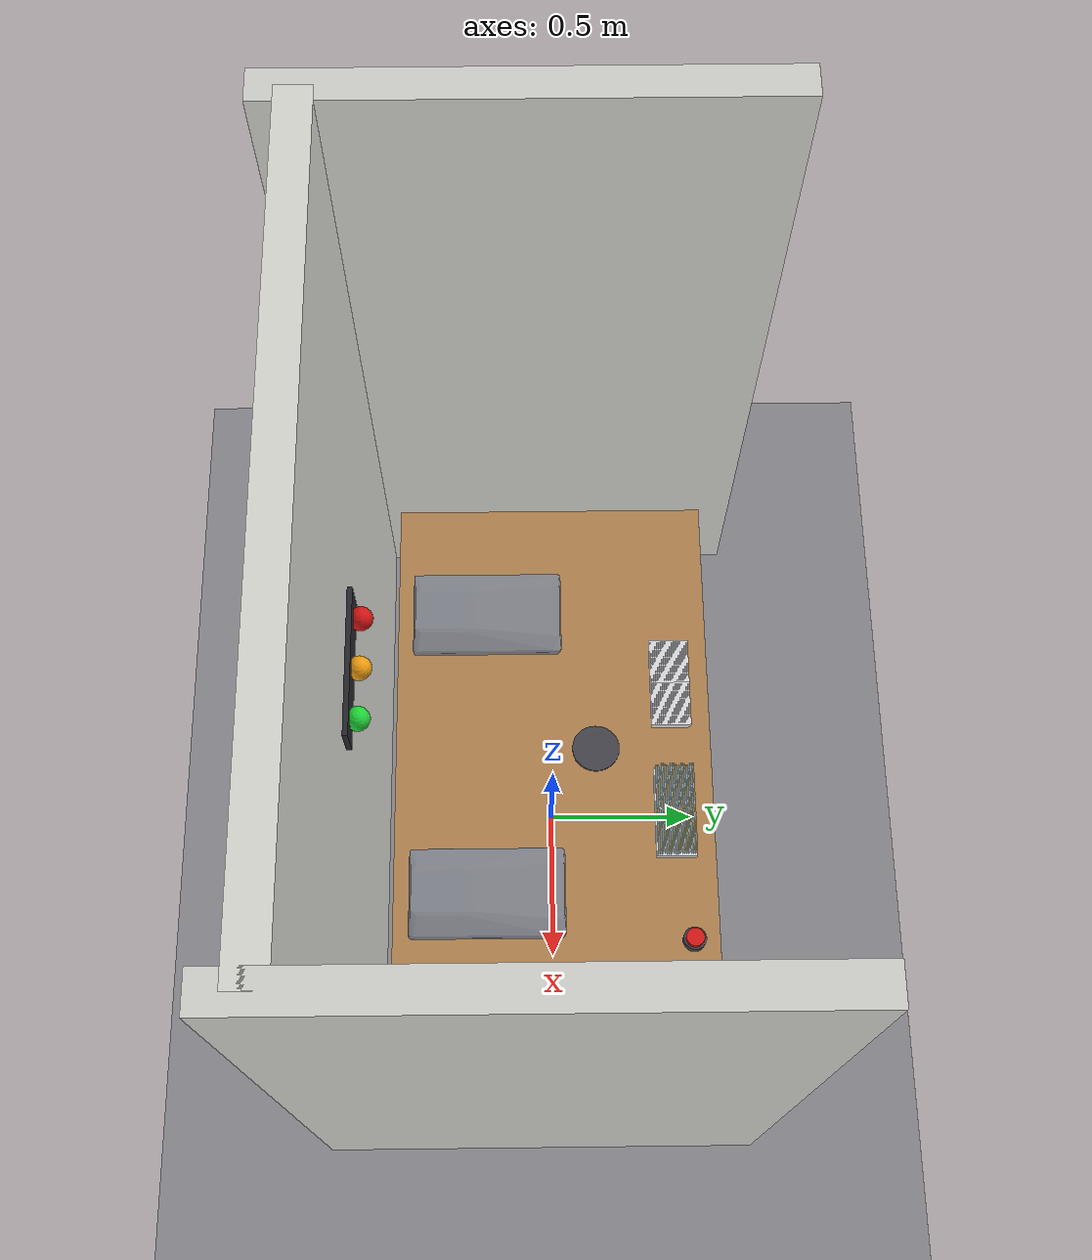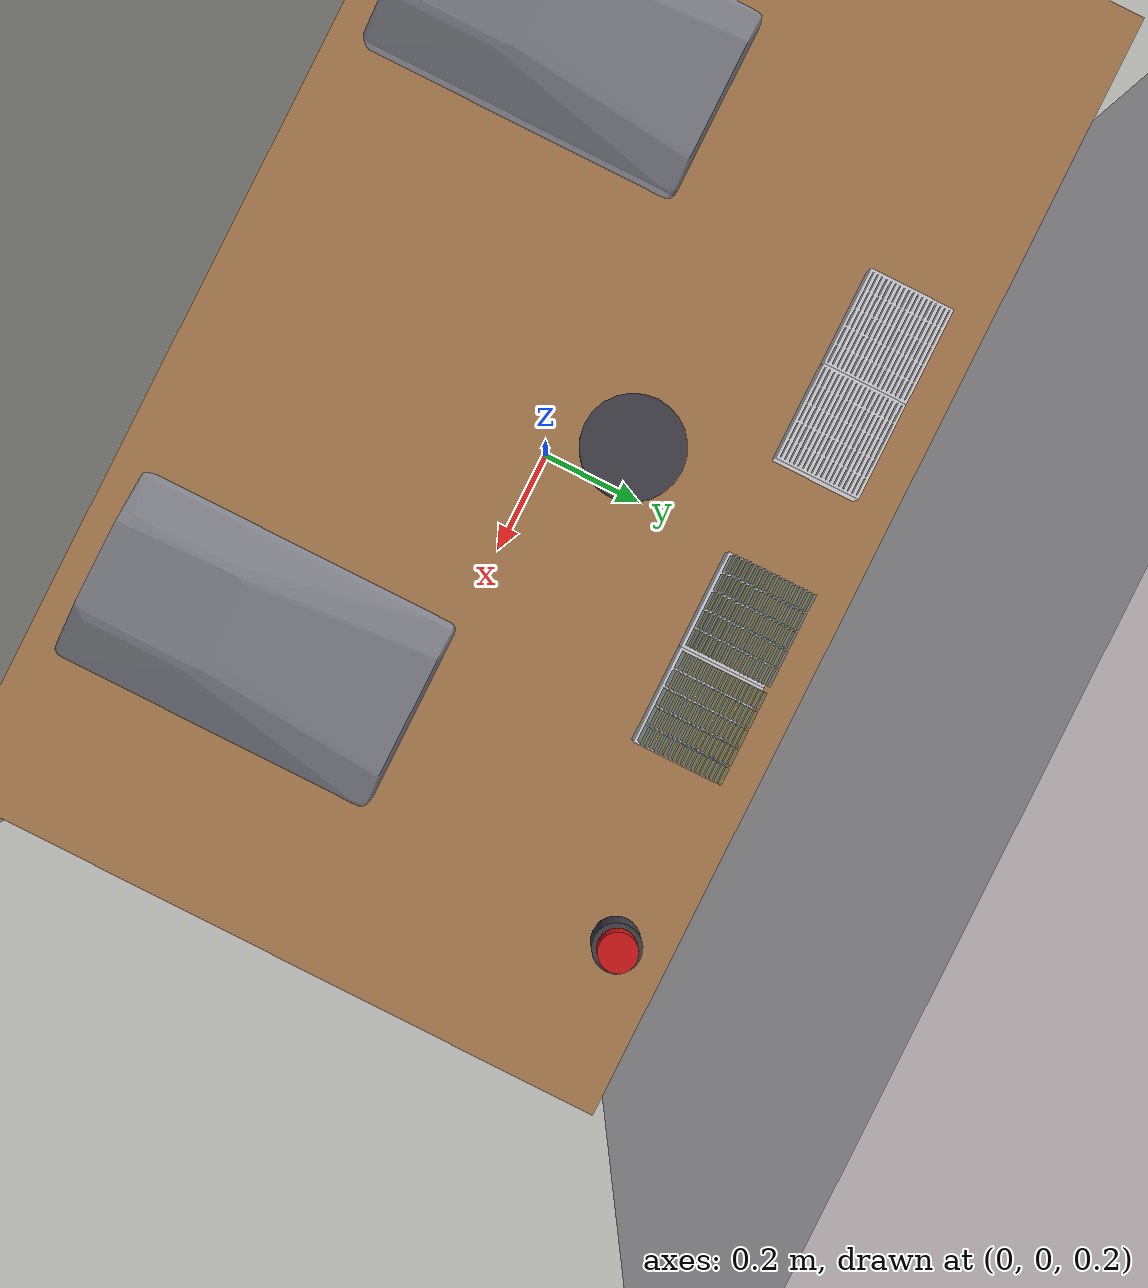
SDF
<?xml version='1.0' encoding='utf-8'?>
<sdf version="1.9">
  <world name="celda_piper">
    <plugin filename="gz-sim-physics-system" name="gz::sim::systems::Physics" />
    <plugin filename="gz-sim-user-commands-system" name="gz::sim::systems::UserCommands" />
    <plugin filename="gz-sim-scene-broadcaster-system" name="gz::sim::systems::SceneBroadcaster" />
    <plugin filename="gz-sim-contact-system" name="gz::sim::systems::Contact" />
    <physics name="1ms" type="ode">
      <max_step_size>0.001</max_step_size>
      <real_time_factor>1.0</real_time_factor>
    </physics>
    <gravity>0 0 -9.8</gravity>
    <scene>
      <ambient>0.55 0.55 0.55 1</ambient>
      <background>0.76 0.79 0.83 1</background>
      <shadows>true</shadows>
    </scene>

    <light type="directional" name="sun">
      <cast_shadows>true</cast_shadows>
      <pose>0 0 4 0 0 0</pose>
      <diffuse>0.9 0.9 0.9 1</diffuse>
      <specular>0.2 0.2 0.2 1</specular>
      <direction>-0.4 0.5 -0.8</direction>
    </light>
    <light type="point" name="lampara_celda">
      <pose>0 0.2 2.2 0 0 0</pose>
      <diffuse>0.55 0.55 0.55 1</diffuse>
      <attenuation>
        <range>8</range>
        <linear>0.2</linear>
      </attenuation>
    </light>

    <!-- Luces de los tres LEDs. Radio corto para que marquen la pared
         sin lavar la escena. Son las que conmuta light_config. -->
    <light type="point" name="led_rojo">
      <pose>-0.15 -0.545 1.45 0 0 0</pose>
      <diffuse>0.50 0.02 0.02 1</diffuse>
      <attenuation><range>0.60</range><linear>0.9</linear><quadratic>1.2</quadratic></attenuation>
    </light>
    <light type="point" name="led_ambar">
      <pose>0 -0.545 1.45 0 0 0</pose>
      <diffuse>0.50 0.30 0.02 1</diffuse>
      <attenuation><range>0.60</range><linear>0.9</linear><quadratic>1.2</quadratic></attenuation>
    </light>
    <light type="point" name="led_verde">
      <pose>0.15 -0.545 1.45 0 0 0</pose>
      <diffuse>0.05 0.50 0.10 1</diffuse>
      <attenuation><range>0.60</range><linear>0.9</linear><quadratic>1.2</quadratic></attenuation>
    </light>

    <model name="ground_plane">
      <static>true</static>
      <link name="link">
        <collision name="collision">
          <geometry><plane><normal>0 0 1</normal><size>20 20</size></plane></geometry>
        </collision>
        <visual name="visual">
          <geometry><plane><normal>0 0 1</normal><size>20 20</size></plane></geometry>
          <material>
            <ambient>0.45 0.45 0.47 1</ambient>
            <diffuse>0.55 0.55 0.57 1</diffuse>
          </material>
        </visual>
      </link>
    </model>

    <model name="pared_trasera">
      <static>true</static>
      <pose>0 -0.63 1.25 0 0 0</pose>
      <link name="link">
        <collision name="collision">
          <geometry><box><size>2.20 0.10 2.50</size></box></geometry>
        </collision>
        <visual name="visual">
          <geometry><box><size>2.20 0.10 2.50</size></box></geometry>
          <material>
            <ambient>0.75 0.75 0.72 1</ambient>
            <diffuse>0.88 0.88 0.85 1</diffuse>
          </material>
        </visual>
      </link>
    </model>

    <model name="pared_izquierda">
      <static>true</static>
      <pose>-1.10 -0.05 1.25 0 0 0</pose>
      <link name="link">
        <collision name="collision">
          <geometry><box><size>0.10 1.40 2.50</size></box></geometry>
        </collision>
        <visual name="visual">
          <geometry><box><size>0.10 1.40 2.50</size></box></geometry>
          <material>
            <ambient>0.72 0.72 0.70 1</ambient>
            <diffuse>0.85 0.85 0.83 1</diffuse>
          </material>
        </visual>
      </link>
    </model>

    <model name="pared_derecha">
      <static>true</static>
      <pose>1.10 -0.05 1.25 0 0 0</pose>
      <link name="link">
        <collision name="collision">
          <geometry><box><size>0.10 1.40 2.50</size></box></geometry>
        </collision>
        <visual name="visual">
          <geometry><box><size>0.10 1.40 2.50</size></box></geometry>
          <material>
            <ambient>0.72 0.72 0.70 1</ambient>
            <diffuse>0.85 0.85 0.83 1</diffuse>
          </material>
        </visual>
      </link>
    </model>

    <!-- ===================== MESA =====================
         1.70 x 1.00 x 0.75. Coincide con el plano sin tocar nada.
         ================================================ -->
    <include>
      <uri>model://mesa</uri>
      <name>mesa</name>
      <pose>0 0 0 0 0 0</pose>
    </include>

    <!-- ===================== MICROSCOPIOS =====================
         yaw 0 = platina hacia el operador. Ver ADVERTENCIAS A y B.
         ========================================================= -->
    <include>
      <uri>model://microscopio_msr</uri>
      <name>microscopio_der</name>
      <pose>-0.4685 -0.21 0.75 0 0 3.14159265</pose>
    </include>
    <include>
      <uri>model://microscopio_msr</uri>
      <name>microscopio_izq</name>
      <pose>0.4685 -0.21 0.75 0 0 3.14159265</pose>
    </include>

    <include>
      <uri>model://rack_laminillas</uri>
      <name>rack_in_1</name>
      <pose>0.28775 0.377 0.75 0 0 0</pose>
    </include>
    <include>
      <uri>model://rack_laminillas_lleno</uri>
      <name>rack_in_2</name>
      <pose>0.14325 0.377 0.75 0 0 0</pose>
    </include>
    <include>
      <uri>model://rack_laminillas</uri>
      <name>rack_out_3</name>
      <pose>-0.14325 0.377 0.75 0 0 0</pose>
    </include>
    <include>
      <uri>model://rack_laminillas</uri>
      <name>rack_out_4</name>
      <pose>-0.28775 0.377 0.75 0 0 0</pose>
    </include>

    <!-- Placa de montaje: disco de 150 mm, el circulo del plano.
         Antes era una caja de 130 x 145 mm. -->
    <model name="placa_estabilizadora">
      <static>true</static>
      <pose>0 0.135 0.754 0 0 0</pose>
      <link name="link">
        <visual name="visual">
          <geometry><cylinder><radius>0.075</radius><length>0.008</length></cylinder></geometry>
          <material>
            <ambient>0.18 0.18 0.20 1</ambient>
            <diffuse>0.28 0.28 0.31 1</diffuse>
          </material>
        </visual>
      </link>
    </model>

    <model name="panel_leds">
      <static>true</static>
      <pose>0 -0.575 1.45 0 0 0</pose>
      <link name="link">
        <visual name="placa">
          <geometry><box><size>0.44 0.02 0.12</size></box></geometry>
          <material>
            <ambient>0.10 0.10 0.11 1</ambient>
            <diffuse>0.16 0.16 0.18 1</diffuse>
          </material>
        </visual>
        <visual name="led_rojo">
          <pose>-0.15 0.03 0 0 0 0</pose>
          <geometry><sphere><radius>0.035</radius></sphere></geometry>
          <material>
            <ambient>0.35 0.03 0.03 1</ambient>
            <diffuse>0.85 0.08 0.08 1</diffuse>
            <emissive>0.65 0.05 0.05 1</emissive>
          </material>
        </visual>
        <visual name="led_ambar">
          <pose>0 0.03 0 0 0 0</pose>
          <geometry><sphere><radius>0.035</radius></sphere></geometry>
          <material>
            <ambient>0.38 0.24 0.02 1</ambient>
            <diffuse>0.95 0.62 0.06 1</diffuse>
            <emissive>0.75 0.48 0.04 1</emissive>
          </material>
        </visual>
        <visual name="led_verde">
          <pose>0.15 0.03 0 0 0 0</pose>
          <geometry><sphere><radius>0.035</radius></sphere></geometry>
          <material>
            <ambient>0.05 0.32 0.08 1</ambient>
            <diffuse>0.12 0.85 0.22 1</diffuse>
            <emissive>0.08 0.62 0.16 1</emissive>
          </material>
        </visual>
      </link>
    </model>

    <model name="boton_operador">
      <static>true</static>
      <pose>0.62 0.42 0.75 0 0 0</pose>
      <link name="link">
        <collision name="collision">
          <pose>0 0 0.024 0 0 0</pose>
          <geometry><cylinder><radius>0.035</radius><length>0.048</length></cylinder></geometry>
        </collision>
        <visual name="base">
          <pose>0 0 0.015 0 0 0</pose>
          <geometry><cylinder><radius>0.035</radius><length>0.030</length></cylinder></geometry>
          <material>
            <ambient>0.16 0.16 0.18 1</ambient>
            <diffuse>0.26 0.26 0.29 1</diffuse>
          </material>
        </visual>
        <visual name="seta">
          <pose>0 0 0.039 0 0 0</pose>
          <geometry><cylinder><radius>0.028</radius><length>0.018</length></cylinder></geometry>
          <material>
            <ambient>0.40 0.04 0.04 1</ambient>
            <diffuse>0.88 0.10 0.10 1</diffuse>
            <specular>0.3 0.3 0.3 1</specular>
          </material>
        </visual>
      </link>
    </model>

    <!-- ##### LAMINILLAS_DINAMICAS_INICIO (generado, no editar) ##### -->
    <include>
      <uri>model://laminilla</uri>
      <name>lam_in_1_c1_f1</name>
      <pose>0.23235 0.31920 0.78990 0 0 1.5708</pose>
    </include>
    <include>
      <uri>model://laminilla</uri>
      <name>lam_in_1_c1_f2</name>
      <pose>0.23235 0.32600 0.78990 0 0 1.5708</pose>
    </include>
    <include>
      <uri>model://laminilla</uri>
      <name>lam_in_1_c1_f3</name>
      <pose>0.23235 0.33280 0.78990 0 0 1.5708</pose>
    </include>
    <include>
      <uri>model://laminilla</uri>
      <name>lam_in_1_c1_f4</name>
      <pose>0.23235 0.33960 0.78990 0 0 1.5708</pose>
    </include>
    <include>
      <uri>model://laminilla</uri>
      <name>lam_in_1_c1_f5</name>
      <pose>0.23235 0.34640 0.78990 0 0 1.5708</pose>
    </include>
    <include>
      <uri>model://laminilla</uri>
      <name>lam_in_1_c1_f6</name>
      <pose>0.23235 0.35320 0.78990 0 0 1.5708</pose>
    </include>
    <include>
      <uri>model://laminilla</uri>
      <name>lam_in_1_c1_f7</name>
      <pose>0.23235 0.36000 0.78990 0 0 1.5708</pose>
    </include>
    <include>
      <uri>model://laminilla</uri>
      <name>lam_in_1_c1_f8</name>
      <pose>0.23235 0.36680 0.78990 0 0 1.5708</pose>
    </include>
    <include>
      <uri>model://laminilla</uri>
      <name>lam_in_1_c1_f9</name>
      <pose>0.23235 0.37360 0.78990 0 0 1.5708</pose>
    </include>
    <include>
      <uri>model://laminilla</uri>
      <name>lam_in_1_c1_f10</name>
      <pose>0.23235 0.38040 0.78990 0 0 1.5708</pose>
    </include>
    <include>
      <uri>model://laminilla</uri>
      <name>lam_in_1_c1_f11</name>
      <pose>0.23235 0.38720 0.78990 0 0 1.5708</pose>
    </include>
    <include>
      <uri>model://laminilla</uri>
      <name>lam_in_1_c1_f12</name>
      <pose>0.23235 0.39400 0.78990 0 0 1.5708</pose>
    </include>
    <include>
      <uri>model://laminilla</uri>
      <name>lam_in_1_c1_f13</name>
      <pose>0.23235 0.40080 0.78990 0 0 1.5708</pose>
    </include>
    <include>
      <uri>model://laminilla</uri>
      <name>lam_in_1_c1_f14</name>
      <pose>0.23235 0.40760 0.78990 0 0 1.5708</pose>
    </include>
    <include>
      <uri>model://laminilla</uri>
      <name>lam_in_1_c1_f15</name>
      <pose>0.23235 0.41440 0.78990 0 0 1.5708</pose>
    </include>
    <include>
      <uri>model://laminilla</uri>
      <name>lam_in_1_c1_f16</name>
      <pose>0.23235 0.42120 0.78990 0 0 1.5708</pose>
    </include>
    <include>
      <uri>model://laminilla</uri>
      <name>lam_in_1_c1_f17</name>
      <pose>0.23235 0.42800 0.78990 0 0 1.5708</pose>
    </include>
    <include>
      <uri>model://laminilla</uri>
      <name>lam_in_1_c1_f18</name>
      <pose>0.23235 0.43480 0.78990 0 0 1.5708</pose>
    </include>
    <include>
      <uri>model://laminilla</uri>
      <name>lam_in_1_c2_f1</name>
      <pose>0.26005 0.31920 0.78990 0 0 1.5708</pose>
    </include>
    <include>
      <uri>model://laminilla</uri>
      <name>lam_in_1_c2_f2</name>
      <pose>0.26005 0.32600 0.78990 0 0 1.5708</pose>
    </include>
    <include>
      <uri>model://laminilla</uri>
      <name>lam_in_1_c2_f3</name>
      <pose>0.26005 0.33280 0.78990 0 0 1.5708</pose>
    </include>
    <include>
      <uri>model://laminilla</uri>
      <name>lam_in_1_c2_f4</name>
      <pose>0.26005 0.33960 0.78990 0 0 1.5708</pose>
    </include>
    <include>
      <uri>model://laminilla</uri>
      <name>lam_in_1_c2_f5</name>
      <pose>0.26005 0.34640 0.78990 0 0 1.5708</pose>
    </include>
    <include>
      <uri>model://laminilla</uri>
      <name>lam_in_1_c2_f6</name>
      <pose>0.26005 0.35320 0.78990 0 0 1.5708</pose>
    </include>
    <include>
      <uri>model://laminilla</uri>
      <name>lam_in_1_c2_f7</name>
      <pose>0.26005 0.36000 0.78990 0 0 1.5708</pose>
    </include>
    <include>
      <uri>model://laminilla</uri>
      <name>lam_in_1_c2_f8</name>
      <pose>0.26005 0.36680 0.78990 0 0 1.5708</pose>
    </include>
    <include>
      <uri>model://laminilla</uri>
      <name>lam_in_1_c2_f9</name>
      <pose>0.26005 0.37360 0.78990 0 0 1.5708</pose>
    </include>
    <include>
      <uri>model://laminilla</uri>
      <name>lam_in_1_c2_f10</name>
      <pose>0.26005 0.38040 0.78990 0 0 1.5708</pose>
    </include>
    <include>
      <uri>model://laminilla</uri>
      <name>lam_in_1_c2_f11</name>
      <pose>0.26005 0.38720 0.78990 0 0 1.5708</pose>
    </include>
    <include>
      <uri>model://laminilla</uri>
      <name>lam_in_1_c2_f12</name>
      <pose>0.26005 0.39400 0.78990 0 0 1.5708</pose>
    </include>
    <include>
      <uri>model://laminilla</uri>
      <name>lam_in_1_c2_f13</name>
      <pose>0.26005 0.40080 0.78990 0 0 1.5708</pose>
    </include>
    <include>
      <uri>model://laminilla</uri>
      <name>lam_in_1_c2_f14</name>
      <pose>0.26005 0.40760 0.78990 0 0 1.5708</pose>
    </include>
    <include>
      <uri>model://laminilla</uri>
      <name>lam_in_1_c2_f15</name>
      <pose>0.26005 0.41440 0.78990 0 0 1.5708</pose>
    </include>
    <include>
      <uri>model://laminilla</uri>
      <name>lam_in_1_c2_f16</name>
      <pose>0.26005 0.42120 0.78990 0 0 1.5708</pose>
    </include>
    <include>
      <uri>model://laminilla</uri>
      <name>lam_in_1_c2_f17</name>
      <pose>0.26005 0.42800 0.78990 0 0 1.5708</pose>
    </include>
    <include>
      <uri>model://laminilla</uri>
      <name>lam_in_1_c2_f18</name>
      <pose>0.26005 0.43480 0.78990 0 0 1.5708</pose>
    </include>
    <include>
      <uri>model://laminilla</uri>
      <name>lam_in_1_c3_f1</name>
      <pose>0.28775 0.31920 0.78990 0 0 1.5708</pose>
    </include>
    <include>
      <uri>model://laminilla</uri>
      <name>lam_in_1_c3_f2</name>
      <pose>0.28775 0.32600 0.78990 0 0 1.5708</pose>
    </include>
    <include>
      <uri>model://laminilla</uri>
      <name>lam_in_1_c3_f3</name>
      <pose>0.28775 0.33280 0.78990 0 0 1.5708</pose>
    </include>
    <include>
      <uri>model://laminilla</uri>
      <name>lam_in_1_c3_f4</name>
      <pose>0.28775 0.33960 0.78990 0 0 1.5708</pose>
    </include>
    <include>
      <uri>model://laminilla</uri>
      <name>lam_in_1_c3_f5</name>
      <pose>0.28775 0.34640 0.78990 0 0 1.5708</pose>
    </include>
    <include>
      <uri>model://laminilla</uri>
      <name>lam_in_1_c3_f6</name>
      <pose>0.28775 0.35320 0.78990 0 0 1.5708</pose>
    </include>
    <include>
      <uri>model://laminilla</uri>
      <name>lam_in_1_c3_f7</name>
      <pose>0.28775 0.36000 0.78990 0 0 1.5708</pose>
    </include>
    <include>
      <uri>model://laminilla</uri>
      <name>lam_in_1_c3_f8</name>
      <pose>0.28775 0.36680 0.78990 0 0 1.5708</pose>
    </include>
    <include>
      <uri>model://laminilla</uri>
      <name>lam_in_1_c3_f9</name>
      <pose>0.28775 0.37360 0.78990 0 0 1.5708</pose>
    </include>
    <include>
      <uri>model://laminilla</uri>
      <name>lam_in_1_c3_f10</name>
      <pose>0.28775 0.38040 0.78990 0 0 1.5708</pose>
    </include>
    <include>
      <uri>model://laminilla</uri>
      <name>lam_in_1_c3_f11</name>
      <pose>0.28775 0.38720 0.78990 0 0 1.5708</pose>
    </include>
    <include>
      <uri>model://laminilla</uri>
      <name>lam_in_1_c3_f12</name>
      <pose>0.28775 0.39400 0.78990 0 0 1.5708</pose>
    </include>
    <include>
      <uri>model://laminilla</uri>
      <name>lam_in_1_c3_f13</name>
      <pose>0.28775 0.40080 0.78990 0 0 1.5708</pose>
    </include>
    <include>
      <uri>model://laminilla</uri>
      <name>lam_in_1_c3_f14</name>
      <pose>0.28775 0.40760 0.78990 0 0 1.5708</pose>
    </include>
    <include>
      <uri>model://laminilla</uri>
      <name>lam_in_1_c3_f15</name>
      <pose>0.28775 0.41440 0.78990 0 0 1.5708</pose>
    </include>
    <include>
      <uri>model://laminilla</uri>
      <name>lam_in_1_c3_f16</name>
      <pose>0.28775 0.42120 0.78990 0 0 1.5708</pose>
    </include>
    <include>
      <uri>model://laminilla</uri>
      <name>lam_in_1_c3_f17</name>
      <pose>0.28775 0.42800 0.78990 0 0 1.5708</pose>
    </include>
    <include>
      <uri>model://laminilla</uri>
      <name>lam_in_1_c3_f18</name>
      <pose>0.28775 0.43480 0.78990 0 0 1.5708</pose>
    </include>
    <include>
      <uri>model://laminilla</uri>
      <name>lam_in_1_c4_f1</name>
      <pose>0.31545 0.31920 0.78990 0 0 1.5708</pose>
    </include>
    <include>
      <uri>model://laminilla</uri>
      <name>lam_in_1_c4_f2</name>
      <pose>0.31545 0.32600 0.78990 0 0 1.5708</pose>
    </include>
    <include>
      <uri>model://laminilla</uri>
      <name>lam_in_1_c4_f3</name>
      <pose>0.31545 0.33280 0.78990 0 0 1.5708</pose>
    </include>
    <include>
      <uri>model://laminilla</uri>
      <name>lam_in_1_c4_f4</name>
      <pose>0.31545 0.33960 0.78990 0 0 1.5708</pose>
    </include>
    <include>
      <uri>model://laminilla</uri>
      <name>lam_in_1_c4_f5</name>
      <pose>0.31545 0.34640 0.78990 0 0 1.5708</pose>
    </include>
    <include>
      <uri>model://laminilla</uri>
      <name>lam_in_1_c4_f6</name>
      <pose>0.31545 0.35320 0.78990 0 0 1.5708</pose>
    </include>
    <include>
      <uri>model://laminilla</uri>
      <name>lam_in_1_c4_f7</name>
      <pose>0.31545 0.36000 0.78990 0 0 1.5708</pose>
    </include>
    <include>
      <uri>model://laminilla</uri>
      <name>lam_in_1_c4_f8</name>
      <pose>0.31545 0.36680 0.78990 0 0 1.5708</pose>
    </include>
    <include>
      <uri>model://laminilla</uri>
      <name>lam_in_1_c4_f9</name>
      <pose>0.31545 0.37360 0.78990 0 0 1.5708</pose>
    </include>
    <include>
      <uri>model://laminilla</uri>
      <name>lam_in_1_c4_f10</name>
      <pose>0.31545 0.38040 0.78990 0 0 1.5708</pose>
    </include>
    <include>
      <uri>model://laminilla</uri>
      <name>lam_in_1_c4_f11</name>
      <pose>0.31545 0.38720 0.78990 0 0 1.5708</pose>
    </include>
    <include>
      <uri>model://laminilla</uri>
      <name>lam_in_1_c4_f12</name>
      <pose>0.31545 0.39400 0.78990 0 0 1.5708</pose>
    </include>
    <include>
      <uri>model://laminilla</uri>
      <name>lam_in_1_c4_f13</name>
      <pose>0.31545 0.40080 0.78990 0 0 1.5708</pose>
    </include>
    <include>
      <uri>model://laminilla</uri>
      <name>lam_in_1_c4_f14</name>
      <pose>0.31545 0.40760 0.78990 0 0 1.5708</pose>
    </include>
    <include>
      <uri>model://laminilla</uri>
      <name>lam_in_1_c4_f15</name>
      <pose>0.31545 0.41440 0.78990 0 0 1.5708</pose>
    </include>
    <include>
      <uri>model://laminilla</uri>
      <name>lam_in_1_c4_f16</name>
      <pose>0.31545 0.42120 0.78990 0 0 1.5708</pose>
    </include>
    <include>
      <uri>model://laminilla</uri>
      <name>lam_in_1_c4_f17</name>
      <pose>0.31545 0.42800 0.78990 0 0 1.5708</pose>
    </include>
    <include>
      <uri>model://laminilla</uri>
      <name>lam_in_1_c4_f18</name>
      <pose>0.31545 0.43480 0.78990 0 0 1.5708</pose>
    </include>
    <include>
      <uri>model://laminilla</uri>
      <name>lam_in_1_c5_f1</name>
      <pose>0.34315 0.31920 0.78990 0 0 1.5708</pose>
    </include>
    <include>
      <uri>model://laminilla</uri>
      <name>lam_in_1_c5_f2</name>
      <pose>0.34315 0.32600 0.78990 0 0 1.5708</pose>
    </include>
    <include>
      <uri>model://laminilla</uri>
      <name>lam_in_1_c5_f3</name>
      <pose>0.34315 0.33280 0.78990 0 0 1.5708</pose>
    </include>
    <include>
      <uri>model://laminilla</uri>
      <name>lam_in_1_c5_f4</name>
      <pose>0.34315 0.33960 0.78990 0 0 1.5708</pose>
    </include>
    <include>
      <uri>model://laminilla</uri>
      <name>lam_in_1_c5_f5</name>
      <pose>0.34315 0.34640 0.78990 0 0 1.5708</pose>
    </include>
    <include>
      <uri>model://laminilla</uri>
      <name>lam_in_1_c5_f6</name>
      <pose>0.34315 0.35320 0.78990 0 0 1.5708</pose>
    </include>
    <include>
      <uri>model://laminilla</uri>
      <name>lam_in_1_c5_f7</name>
      <pose>0.34315 0.36000 0.78990 0 0 1.5708</pose>
    </include>
    <include>
      <uri>model://laminilla</uri>
      <name>lam_in_1_c5_f8</name>
      <pose>0.34315 0.36680 0.78990 0 0 1.5708</pose>
    </include>
    <include>
      <uri>model://laminilla</uri>
      <name>lam_in_1_c5_f9</name>
      <pose>0.34315 0.37360 0.78990 0 0 1.5708</pose>
    </include>
    <include>
      <uri>model://laminilla</uri>
      <name>lam_in_1_c5_f10</name>
      <pose>0.34315 0.38040 0.78990 0 0 1.5708</pose>
    </include>
    <include>
      <uri>model://laminilla</uri>
      <name>lam_in_1_c5_f11</name>
      <pose>0.34315 0.38720 0.78990 0 0 1.5708</pose>
    </include>
    <include>
      <uri>model://laminilla</uri>
      <name>lam_in_1_c5_f12</name>
      <pose>0.34315 0.39400 0.78990 0 0 1.5708</pose>
    </include>
    <include>
      <uri>model://laminilla</uri>
      <name>lam_in_1_c5_f13</name>
      <pose>0.34315 0.40080 0.78990 0 0 1.5708</pose>
    </include>
    <include>
      <uri>model://laminilla</uri>
      <name>lam_in_1_c5_f14</name>
      <pose>0.34315 0.40760 0.78990 0 0 1.5708</pose>
    </include>
    <include>
      <uri>model://laminilla</uri>
      <name>lam_in_1_c5_f15</name>
      <pose>0.34315 0.41440 0.78990 0 0 1.5708</pose>
    </include>
    <include>
      <uri>model://laminilla</uri>
      <name>lam_in_1_c5_f16</name>
      <pose>0.34315 0.42120 0.78990 0 0 1.5708</pose>
    </include>
    <include>
      <uri>model://laminilla</uri>
      <name>lam_in_1_c5_f17</name>
      <pose>0.34315 0.42800 0.78990 0 0 1.5708</pose>
    </include>
    <include>
      <uri>model://laminilla</uri>
      <name>lam_in_1_c5_f18</name>
      <pose>0.34315 0.43480 0.78990 0 0 1.5708</pose>
    </include>
    <!-- ##### LAMINILLAS_DINAMICAS_FIN ##### -->

  </world>
</sdf>

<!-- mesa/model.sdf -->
<sdf version="1.7">
  <model name="mesa">

    <static>true</static>

    <link name="link">

      <collision name="tablero_collision">
        <pose>0 0 0.73 0 0 0</pose>
        <geometry>
          <box>
            <size>1.70 1.00 0.04</size>
          </box>
        </geometry>
        <surface>
          <friction>
            <ode>
              <mu>0.8</mu>
              <mu2>0.8</mu2>
            </ode>
          </friction>
        </surface>
      </collision>

      <visual name="tablero_visual">
        <pose>0 0 0.73 0 0 0</pose>
        <geometry>
          <box>
            <size>1.70 1.00 0.04</size>
          </box>
        </geometry>
        <material>
          <ambient>0.62 0.45 0.28 1</ambient>
          <diffuse>0.72 0.53 0.33 1</diffuse>
          <specular>0.15 0.15 0.15 1</specular>
        </material>
      </visual>

      <!-- Pata 1: delantera izquierda -->
      <collision name="pata_1_collision">
        <pose>0.775 0.425 0.355 0 0 0</pose>
        <geometry>
          <box><size>0.05 0.05 0.71</size></box>
        </geometry>
      </collision>
      <visual name="pata_1_visual">
        <pose>0.775 0.425 0.355 0 0 0</pose>
        <geometry>
          <box><size>0.05 0.05 0.71</size></box>
        </geometry>
        <material>
          <ambient>0.35 0.35 0.38 1</ambient>
          <diffuse>0.45 0.45 0.48 1</diffuse>
        </material>
      </visual>

      <!-- Pata 2: delantera derecha -->
      <collision name="pata_2_collision">
        <pose>0.775 -0.425 0.355 0 0 0</pose>
        <geometry>
          <box><size>0.05 0.05 0.71</size></box>
        </geometry>
      </collision>
      <visual name="pata_2_visual">
        <pose>0.775 -0.425 0.355 0 0 0</pose>
        <geometry>
          <box><size>0.05 0.05 0.71</size></box>
        </geometry>
        <material>
          <ambient>0.35 0.35 0.38 1</ambient>
          <diffuse>0.45 0.45 0.48 1</diffuse>
        </material>
      </visual>

      <!-- Pata 3: trasera izquierda -->
      <collision name="pata_3_collision">
        <pose>-0.775 0.425 0.355 0 0 0</pose>
        <geometry>
          <box><size>0.05 0.05 0.71</size></box>
        </geometry>
      </collision>
      <visual name="pata_3_visual">
        <pose>-0.775 0.425 0.355 0 0 0</pose>
        <geometry>
          <box><size>0.05 0.05 0.71</size></box>
        </geometry>
        <material>
          <ambient>0.35 0.35 0.38 1</ambient>
          <diffuse>0.45 0.45 0.48 1</diffuse>
        </material>
      </visual>

      <!-- Pata 4: trasera derecha -->
      <collision name="pata_4_collision">
        <pose>-0.775 -0.425 0.355 0 0 0</pose>
        <geometry>
          <box><size>0.05 0.05 0.71</size></box>
        </geometry>
      </collision>
      <visual name="pata_4_visual">
        <pose>-0.775 -0.425 0.355 0 0 0</pose>
        <geometry>
          <box><size>0.05 0.05 0.71</size></box>
        </geometry>
        <material>
          <ambient>0.35 0.35 0.38 1</ambient>
          <diffuse>0.45 0.45 0.48 1</diffuse>
        </material>
      </visual>

    </link>
  </model>
</sdf>

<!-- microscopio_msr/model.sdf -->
<sdf version="1.7">
  <model name="microscopio_msr">
    <static>true</static>
    <link name="link">
      <!-- ===== VISUAL: malla real del STEP =====
           781k facetas. Escala 0.001 porque la malla esta en mm. -->
      <visual name="malla_detallada">
        <geometry>
          <mesh>
            <uri>model://microscopio_msr/meshes/microscopio_visual.stl</uri>
            <scale>0.001 0.001 0.001</scale>
          </mesh>
        </geometry>
        <material>
          <ambient>0.30 0.30 0.32 1</ambient>
          <diffuse>0.52 0.53 0.56 1</diffuse>
          <specular>0.25 0.25 0.28 1</specular>
        </material>
      </visual>
      <!-- ================================================
           COLISION: 16 cajas
           Nombradas por la parte que representan.
           ================================================ -->
      <!-- Enfoque X-LDA025A, POR DEBAJO de la mesa -->
      <!-- Placa base 475 x 275 -->
      <!-- Platina X-ASR100B120B en posicion centrada -->
      <!-- Envolvente barrida, solo visual -->
      <!-- Eje optico, verificado en X = 0, Y = 0 -->
      <collision name="conv_00">
        <geometry>
          <mesh>
            <uri>model://microscopio_msr/meshes/collision/col_00.stl</uri>
            <scale>0.001 0.001 0.001</scale>
          </mesh>
        </geometry>
        <surface>
          <contact>
            <collide_bitmask>0x01</collide_bitmask>
          </contact>
        </surface>
      </collision>
      <collision name="conv_01">
        <geometry>
          <mesh>
            <uri>model://microscopio_msr/meshes/collision/col_01.stl</uri>
            <scale>0.001 0.001 0.001</scale>
          </mesh>
        </geometry>
        <surface>
          <contact>
            <collide_bitmask>0x01</collide_bitmask>
          </contact>
        </surface>
      </collision>
      <collision name="conv_02">
        <geometry>
          <mesh>
            <uri>model://microscopio_msr/meshes/collision/col_02.stl</uri>
            <scale>0.001 0.001 0.001</scale>
          </mesh>
        </geometry>
        <surface>
          <contact>
            <collide_bitmask>0x01</collide_bitmask>
          </contact>
        </surface>
      </collision>
      <collision name="conv_03">
        <geometry>
          <mesh>
            <uri>model://microscopio_msr/meshes/collision/col_03.stl</uri>
            <scale>0.001 0.001 0.001</scale>
          </mesh>
        </geometry>
        <surface>
          <contact>
            <collide_bitmask>0x01</collide_bitmask>
          </contact>
        </surface>
      </collision>
      <collision name="conv_04">
        <geometry>
          <mesh>
            <uri>model://microscopio_msr/meshes/collision/col_04.stl</uri>
            <scale>0.001 0.001 0.001</scale>
          </mesh>
        </geometry>
        <surface>
          <contact>
            <collide_bitmask>0x01</collide_bitmask>
          </contact>
        </surface>
      </collision>
      <collision name="conv_05">
        <geometry>
          <mesh>
            <uri>model://microscopio_msr/meshes/collision/col_05.stl</uri>
            <scale>0.001 0.001 0.001</scale>
          </mesh>
        </geometry>
        <surface>
          <contact>
            <collide_bitmask>0x01</collide_bitmask>
          </contact>
        </surface>
      </collision>
      <collision name="conv_06">
        <geometry>
          <mesh>
            <uri>model://microscopio_msr/meshes/collision/col_06.stl</uri>
            <scale>0.001 0.001 0.001</scale>
          </mesh>
        </geometry>
        <surface>
          <contact>
            <collide_bitmask>0x01</collide_bitmask>
          </contact>
        </surface>
      </collision>
      <collision name="conv_07">
        <geometry>
          <mesh>
            <uri>model://microscopio_msr/meshes/collision/col_07.stl</uri>
            <scale>0.001 0.001 0.001</scale>
          </mesh>
        </geometry>
        <surface>
          <contact>
            <collide_bitmask>0x01</collide_bitmask>
          </contact>
        </surface>
      </collision>
      <collision name="conv_08">
        <geometry>
          <mesh>
            <uri>model://microscopio_msr/meshes/collision/col_08.stl</uri>
            <scale>0.001 0.001 0.001</scale>
          </mesh>
        </geometry>
        <surface>
          <contact>
            <collide_bitmask>0x01</collide_bitmask>
          </contact>
        </surface>
      </collision>
      <collision name="conv_09">
        <geometry>
          <mesh>
            <uri>model://microscopio_msr/meshes/collision/col_09.stl</uri>
            <scale>0.001 0.001 0.001</scale>
          </mesh>
        </geometry>
        <surface>
          <contact>
            <collide_bitmask>0x01</collide_bitmask>
          </contact>
        </surface>
      </collision>
      <collision name="conv_10">
        <geometry>
          <mesh>
            <uri>model://microscopio_msr/meshes/collision/col_10.stl</uri>
            <scale>0.001 0.001 0.001</scale>
          </mesh>
        </geometry>
        <surface>
          <contact>
            <collide_bitmask>0x01</collide_bitmask>
          </contact>
        </surface>
      </collision>
      <collision name="conv_11">
        <geometry>
          <mesh>
            <uri>model://microscopio_msr/meshes/collision/col_11.stl</uri>
            <scale>0.001 0.001 0.001</scale>
          </mesh>
        </geometry>
        <surface>
          <contact>
            <collide_bitmask>0x01</collide_bitmask>
          </contact>
        </surface>
      </collision>
      <collision name="conv_12">
        <geometry>
          <mesh>
            <uri>model://microscopio_msr/meshes/collision/col_12.stl</uri>
            <scale>0.001 0.001 0.001</scale>
          </mesh>
        </geometry>
        <surface>
          <contact>
            <collide_bitmask>0x01</collide_bitmask>
          </contact>
        </surface>
      </collision>
      <collision name="conv_13">
        <geometry>
          <mesh>
            <uri>model://microscopio_msr/meshes/collision/col_13.stl</uri>
            <scale>0.001 0.001 0.001</scale>
          </mesh>
        </geometry>
        <surface>
          <contact>
            <collide_bitmask>0x01</collide_bitmask>
          </contact>
        </surface>
      </collision>
      <collision name="conv_14">
        <geometry>
          <mesh>
            <uri>model://microscopio_msr/meshes/collision/col_14.stl</uri>
            <scale>0.001 0.001 0.001</scale>
          </mesh>
        </geometry>
        <surface>
          <contact>
            <collide_bitmask>0x01</collide_bitmask>
          </contact>
        </surface>
      </collision>
      <collision name="conv_15">
        <geometry>
          <mesh>
            <uri>model://microscopio_msr/meshes/collision/col_15.stl</uri>
            <scale>0.001 0.001 0.001</scale>
          </mesh>
        </geometry>
        <surface>
          <contact>
            <collide_bitmask>0x01</collide_bitmask>
          </contact>
        </surface>
      </collision>
      <collision name="conv_16">
        <geometry>
          <mesh>
            <uri>model://microscopio_msr/meshes/collision/col_16.stl</uri>
            <scale>0.001 0.001 0.001</scale>
          </mesh>
        </geometry>
        <surface>
          <contact>
            <collide_bitmask>0x01</collide_bitmask>
          </contact>
        </surface>
      </collision>
      <collision name="conv_17">
        <geometry>
          <mesh>
            <uri>model://microscopio_msr/meshes/collision/col_17.stl</uri>
            <scale>0.001 0.001 0.001</scale>
          </mesh>
        </geometry>
        <surface>
          <contact>
            <collide_bitmask>0x01</collide_bitmask>
          </contact>
        </surface>
      </collision>
      <collision name="conv_18">
        <geometry>
          <mesh>
            <uri>model://microscopio_msr/meshes/collision/col_18.stl</uri>
            <scale>0.001 0.001 0.001</scale>
          </mesh>
        </geometry>
        <surface>
          <contact>
            <collide_bitmask>0x01</collide_bitmask>
          </contact>
        </surface>
      </collision>
      <collision name="conv_19">
        <geometry>
          <mesh>
            <uri>model://microscopio_msr/meshes/collision/col_19.stl</uri>
            <scale>0.001 0.001 0.001</scale>
          </mesh>
        </geometry>
        <surface>
          <contact>
            <collide_bitmask>0x01</collide_bitmask>
          </contact>
        </surface>
      </collision>
      <collision name="conv_20">
        <geometry>
          <mesh>
            <uri>model://microscopio_msr/meshes/collision/col_20.stl</uri>
            <scale>0.001 0.001 0.001</scale>
          </mesh>
        </geometry>
        <surface>
          <contact>
            <collide_bitmask>0x01</collide_bitmask>
          </contact>
        </surface>
      </collision>
      <collision name="conv_21">
        <geometry>
          <mesh>
            <uri>model://microscopio_msr/meshes/collision/col_21.stl</uri>
            <scale>0.001 0.001 0.001</scale>
          </mesh>
        </geometry>
        <surface>
          <contact>
            <collide_bitmask>0x01</collide_bitmask>
          </contact>
        </surface>
      </collision>
      <collision name="conv_22">
        <geometry>
          <mesh>
            <uri>model://microscopio_msr/meshes/collision/col_22.stl</uri>
            <scale>0.001 0.001 0.001</scale>
          </mesh>
        </geometry>
        <surface>
          <contact>
            <collide_bitmask>0x01</collide_bitmask>
          </contact>
        </surface>
      </collision>
      <collision name="conv_23">
        <geometry>
          <mesh>
            <uri>model://microscopio_msr/meshes/collision/col_23.stl</uri>
            <scale>0.001 0.001 0.001</scale>
          </mesh>
        </geometry>
        <surface>
          <contact>
            <collide_bitmask>0x01</collide_bitmask>
          </contact>
        </surface>
      </collision>
      <collision name="conv_24">
        <geometry>
          <mesh>
            <uri>model://microscopio_msr/meshes/collision/col_24.stl</uri>
            <scale>0.001 0.001 0.001</scale>
          </mesh>
        </geometry>
        <surface>
          <contact>
            <collide_bitmask>0x01</collide_bitmask>
          </contact>
        </surface>
      </collision>
      <collision name="conv_25">
        <geometry>
          <mesh>
            <uri>model://microscopio_msr/meshes/collision/col_25.stl</uri>
            <scale>0.001 0.001 0.001</scale>
          </mesh>
        </geometry>
        <surface>
          <contact>
            <collide_bitmask>0x01</collide_bitmask>
          </contact>
        </surface>
      </collision>
      <collision name="conv_26">
        <geometry>
          <mesh>
            <uri>model://microscopio_msr/meshes/collision/col_26.stl</uri>
            <scale>0.001 0.001 0.001</scale>
          </mesh>
        </geometry>
        <surface>
          <contact>
            <collide_bitmask>0x01</collide_bitmask>
          </contact>
        </surface>
      </collision>
      <collision name="conv_27">
        <geometry>
          <mesh>
            <uri>model://microscopio_msr/meshes/collision/col_27.stl</uri>
            <scale>0.001 0.001 0.001</scale>
          </mesh>
        </geometry>
        <surface>
          <contact>
            <collide_bitmask>0x01</collide_bitmask>
          </contact>
        </surface>
      </collision>
      <collision name="conv_28">
        <geometry>
          <mesh>
            <uri>model://microscopio_msr/meshes/collision/col_28.stl</uri>
            <scale>0.001 0.001 0.001</scale>
          </mesh>
        </geometry>
        <surface>
          <contact>
            <collide_bitmask>0x01</collide_bitmask>
          </contact>
        </surface>
      </collision>
      <collision name="conv_29">
        <geometry>
          <mesh>
            <uri>model://microscopio_msr/meshes/collision/col_29.stl</uri>
            <scale>0.001 0.001 0.001</scale>
          </mesh>
        </geometry>
        <surface>
          <contact>
            <collide_bitmask>0x01</collide_bitmask>
          </contact>
        </surface>
      </collision>
      <collision name="conv_30">
        <geometry>
          <mesh>
            <uri>model://microscopio_msr/meshes/collision/col_30.stl</uri>
            <scale>0.001 0.001 0.001</scale>
          </mesh>
        </geometry>
        <surface>
          <contact>
            <collide_bitmask>0x01</collide_bitmask>
          </contact>
        </surface>
      </collision>
      <collision name="conv_31">
        <geometry>
          <mesh>
            <uri>model://microscopio_msr/meshes/collision/col_31.stl</uri>
            <scale>0.001 0.001 0.001</scale>
          </mesh>
        </geometry>
        <surface>
          <contact>
            <collide_bitmask>0x01</collide_bitmask>
          </contact>
        </surface>
      </collision>
      <collision name="conv_32">
        <geometry>
          <mesh>
            <uri>model://microscopio_msr/meshes/collision/col_32.stl</uri>
            <scale>0.001 0.001 0.001</scale>
          </mesh>
        </geometry>
        <surface>
          <contact>
            <collide_bitmask>0x01</collide_bitmask>
          </contact>
        </surface>
      </collision>
      <collision name="conv_33">
        <geometry>
          <mesh>
            <uri>model://microscopio_msr/meshes/collision/col_33.stl</uri>
            <scale>0.001 0.001 0.001</scale>
          </mesh>
        </geometry>
        <surface>
          <contact>
            <collide_bitmask>0x01</collide_bitmask>
          </contact>
        </surface>
      </collision>
      <collision name="conv_34">
        <geometry>
          <mesh>
            <uri>model://microscopio_msr/meshes/collision/col_34.stl</uri>
            <scale>0.001 0.001 0.001</scale>
          </mesh>
        </geometry>
        <surface>
          <contact>
            <collide_bitmask>0x01</collide_bitmask>
          </contact>
        </surface>
      </collision>
      <collision name="conv_35">
        <geometry>
          <mesh>
            <uri>model://microscopio_msr/meshes/collision/col_35.stl</uri>
            <scale>0.001 0.001 0.001</scale>
          </mesh>
        </geometry>
        <surface>
          <contact>
            <collide_bitmask>0x01</collide_bitmask>
          </contact>
        </surface>
      </collision>
      <collision name="conv_36">
        <geometry>
          <mesh>
            <uri>model://microscopio_msr/meshes/collision/col_36.stl</uri>
            <scale>0.001 0.001 0.001</scale>
          </mesh>
        </geometry>
        <surface>
          <contact>
            <collide_bitmask>0x01</collide_bitmask>
          </contact>
        </surface>
      </collision>
      <collision name="conv_37">
        <geometry>
          <mesh>
            <uri>model://microscopio_msr/meshes/collision/col_37.stl</uri>
            <scale>0.001 0.001 0.001</scale>
          </mesh>
        </geometry>
        <surface>
          <contact>
            <collide_bitmask>0x01</collide_bitmask>
          </contact>
        </surface>
      </collision>
      <collision name="conv_38">
        <geometry>
          <mesh>
            <uri>model://microscopio_msr/meshes/collision/col_38.stl</uri>
            <scale>0.001 0.001 0.001</scale>
          </mesh>
        </geometry>
        <surface>
          <contact>
            <collide_bitmask>0x01</collide_bitmask>
          </contact>
        </surface>
      </collision>
      <collision name="conv_39">
        <geometry>
          <mesh>
            <uri>model://microscopio_msr/meshes/collision/col_39.stl</uri>
            <scale>0.001 0.001 0.001</scale>
          </mesh>
        </geometry>
        <surface>
          <contact>
            <collide_bitmask>0x01</collide_bitmask>
          </contact>
        </surface>
      </collision>
      <collision name="conv_40">
        <geometry>
          <mesh>
            <uri>model://microscopio_msr/meshes/collision/col_40.stl</uri>
            <scale>0.001 0.001 0.001</scale>
          </mesh>
        </geometry>
        <surface>
          <contact>
            <collide_bitmask>0x01</collide_bitmask>
          </contact>
        </surface>
      </collision>
      <collision name="conv_41">
        <geometry>
          <mesh>
            <uri>model://microscopio_msr/meshes/collision/col_41.stl</uri>
            <scale>0.001 0.001 0.001</scale>
          </mesh>
        </geometry>
        <surface>
          <contact>
            <collide_bitmask>0x01</collide_bitmask>
          </contact>
        </surface>
      </collision>
      <collision name="conv_42">
        <geometry>
          <mesh>
            <uri>model://microscopio_msr/meshes/collision/col_42.stl</uri>
            <scale>0.001 0.001 0.001</scale>
          </mesh>
        </geometry>
        <surface>
          <contact>
            <collide_bitmask>0x01</collide_bitmask>
          </contact>
        </surface>
      </collision>
      <collision name="conv_43">
        <geometry>
          <mesh>
            <uri>model://microscopio_msr/meshes/collision/col_43.stl</uri>
            <scale>0.001 0.001 0.001</scale>
          </mesh>
        </geometry>
        <surface>
          <contact>
            <collide_bitmask>0x01</collide_bitmask>
          </contact>
        </surface>
      </collision>
      <collision name="conv_44">
        <geometry>
          <mesh>
            <uri>model://microscopio_msr/meshes/collision/col_44.stl</uri>
            <scale>0.001 0.001 0.001</scale>
          </mesh>
        </geometry>
        <surface>
          <contact>
            <collide_bitmask>0x01</collide_bitmask>
          </contact>
        </surface>
      </collision>
      <collision name="conv_45">
        <geometry>
          <mesh>
            <uri>model://microscopio_msr/meshes/collision/col_45.stl</uri>
            <scale>0.001 0.001 0.001</scale>
          </mesh>
        </geometry>
        <surface>
          <contact>
            <collide_bitmask>0x01</collide_bitmask>
          </contact>
        </surface>
      </collision>
      <collision name="conv_46">
        <geometry>
          <mesh>
            <uri>model://microscopio_msr/meshes/collision/col_46.stl</uri>
            <scale>0.001 0.001 0.001</scale>
          </mesh>
        </geometry>
        <surface>
          <contact>
            <collide_bitmask>0x01</collide_bitmask>
          </contact>
        </surface>
      </collision>
      <collision name="conv_47">
        <geometry>
          <mesh>
            <uri>model://microscopio_msr/meshes/collision/col_47.stl</uri>
            <scale>0.001 0.001 0.001</scale>
          </mesh>
        </geometry>
        <surface>
          <contact>
            <collide_bitmask>0x01</collide_bitmask>
          </contact>
        </surface>
      </collision>
    </link>
  </model>
</sdf>

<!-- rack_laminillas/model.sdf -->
<sdf version="1.7">
  <model name="rack_laminillas">
    <static>true</static>
    <link name="link">

      <collision name="col_base">
        <pose>0.00000 0.00000 0.00100 0 0 0</pose>
        <geometry>
          <box><size>0.14450 0.12560 0.00200</size></box>
        </geometry>
        <surface>
          <friction><ode><mu>0.9</mu><mu2>0.9</mu2></ode></friction>
          <contact>
            <ode><kp>1e6</kp><kd>100</kd><min_depth>0.0002</min_depth></ode>
          </contact>
        </surface>
      </collision>

      <collision name="col_nervio_y_00">
        <pose>0.00000 -0.06080 0.01450 0 0 0</pose>
        <geometry>
          <box><size>0.14450 0.00400 0.02500</size></box>
        </geometry>
        <surface>
          <friction><ode><mu>0.9</mu><mu2>0.9</mu2></ode></friction>
          <contact>
            <ode><kp>1e6</kp><kd>100</kd><min_depth>0.0002</min_depth></ode>
          </contact>
        </surface>
      </collision>

      <collision name="col_nervio_y_01">
        <pose>0.00000 -0.05440 0.01450 0 0 0</pose>
        <geometry>
          <box><size>0.14450 0.00480 0.02500</size></box>
        </geometry>
        <surface>
          <friction><ode><mu>0.9</mu><mu2>0.9</mu2></ode></friction>
          <contact>
            <ode><kp>1e6</kp><kd>100</kd><min_depth>0.0002</min_depth></ode>
          </contact>
        </surface>
      </collision>

      <collision name="col_nervio_y_02">
        <pose>0.00000 -0.04760 0.01450 0 0 0</pose>
        <geometry>
          <box><size>0.14450 0.00480 0.02500</size></box>
        </geometry>
        <surface>
          <friction><ode><mu>0.9</mu><mu2>0.9</mu2></ode></friction>
          <contact>
            <ode><kp>1e6</kp><kd>100</kd><min_depth>0.0002</min_depth></ode>
          </contact>
        </surface>
      </collision>

      <collision name="col_nervio_y_03">
        <pose>0.00000 -0.04080 0.01450 0 0 0</pose>
        <geometry>
          <box><size>0.14450 0.00480 0.02500</size></box>
        </geometry>
        <surface>
          <friction><ode><mu>0.9</mu><mu2>0.9</mu2></ode></friction>
          <contact>
            <ode><kp>1e6</kp><kd>100</kd><min_depth>0.0002</min_depth></ode>
          </contact>
        </surface>
      </collision>

      <collision name="col_nervio_y_04">
        <pose>0.00000 -0.03400 0.01450 0 0 0</pose>
        <geometry>
          <box><size>0.14450 0.00480 0.02500</size></box>
        </geometry>
        <surface>
          <friction><ode><mu>0.9</mu><mu2>0.9</mu2></ode></friction>
          <contact>
            <ode><kp>1e6</kp><kd>100</kd><min_depth>0.0002</min_depth></ode>
          </contact>
        </surface>
      </collision>

      <collision name="col_nervio_y_05">
        <pose>0.00000 -0.02720 0.01450 0 0 0</pose>
        <geometry>
          <box><size>0.14450 0.00480 0.02500</size></box>
        </geometry>
        <surface>
          <friction><ode><mu>0.9</mu><mu2>0.9</mu2></ode></friction>
          <contact>
            <ode><kp>1e6</kp><kd>100</kd><min_depth>0.0002</min_depth></ode>
          </contact>
        </surface>
      </collision>

      <collision name="col_nervio_y_06">
        <pose>0.00000 -0.02040 0.01450 0 0 0</pose>
        <geometry>
          <box><size>0.14450 0.00480 0.02500</size></box>
        </geometry>
        <surface>
          <friction><ode><mu>0.9</mu><mu2>0.9</mu2></ode></friction>
          <contact>
            <ode><kp>1e6</kp><kd>100</kd><min_depth>0.0002</min_depth></ode>
          </contact>
        </surface>
      </collision>

      <collision name="col_nervio_y_07">
        <pose>0.00000 -0.01360 0.01450 0 0 0</pose>
        <geometry>
          <box><size>0.14450 0.00480 0.02500</size></box>
        </geometry>
        <surface>
          <friction><ode><mu>0.9</mu><mu2>0.9</mu2></ode></friction>
          <contact>
            <ode><kp>1e6</kp><kd>100</kd><min_depth>0.0002</min_depth></ode>
          </contact>
        </surface>
      </collision>

      <collision name="col_nervio_y_08">
        <pose>0.00000 -0.00680 0.01450 0 0 0</pose>
        <geometry>
          <box><size>0.14450 0.00480 0.02500</size></box>
        </geometry>
        <surface>
          <friction><ode><mu>0.9</mu><mu2>0.9</mu2></ode></friction>
          <contact>
            <ode><kp>1e6</kp><kd>100</kd><min_depth>0.0002</min_depth></ode>
          </contact>
        </surface>
      </collision>

      <collision name="col_nervio_y_09">
        <pose>0.00000 0.00000 0.01450 0 0 0</pose>
        <geometry>
          <box><size>0.14450 0.00480 0.02500</size></box>
        </geometry>
        <surface>
          <friction><ode><mu>0.9</mu><mu2>0.9</mu2></ode></friction>
          <contact>
            <ode><kp>1e6</kp><kd>100</kd><min_depth>0.0002</min_depth></ode>
          </contact>
        </surface>
      </collision>

      <collision name="col_nervio_y_10">
        <pose>0.00000 0.00680 0.01450 0 0 0</pose>
        <geometry>
          <box><size>0.14450 0.00480 0.02500</size></box>
        </geometry>
        <surface>
          <friction><ode><mu>0.9</mu><mu2>0.9</mu2></ode></friction>
          <contact>
            <ode><kp>1e6</kp><kd>100</kd><min_depth>0.0002</min_depth></ode>
          </contact>
        </surface>
      </collision>

      <collision name="col_nervio_y_11">
        <pose>0.00000 0.01360 0.01450 0 0 0</pose>
        <geometry>
          <box><size>0.14450 0.00480 0.02500</size></box>
        </geometry>
        <surface>
          <friction><ode><mu>0.9</mu><mu2>0.9</mu2></ode></friction>
          <contact>
            <ode><kp>1e6</kp><kd>100</kd><min_depth>0.0002</min_depth></ode>
          </contact>
        </surface>
      </collision>

      <collision name="col_nervio_y_12">
        <pose>0.00000 0.02040 0.01450 0 0 0</pose>
        <geometry>
          <box><size>0.14450 0.00480 0.02500</size></box>
        </geometry>
        <surface>
          <friction><ode><mu>0.9</mu><mu2>0.9</mu2></ode></friction>
          <contact>
            <ode><kp>1e6</kp><kd>100</kd><min_depth>0.0002</min_depth></ode>
          </contact>
        </surface>
      </collision>

      <collision name="col_nervio_y_13">
        <pose>0.00000 0.02720 0.01450 0 0 0</pose>
        <geometry>
          <box><size>0.14450 0.00480 0.02500</size></box>
        </geometry>
        <surface>
          <friction><ode><mu>0.9</mu><mu2>0.9</mu2></ode></friction>
          <contact>
            <ode><kp>1e6</kp><kd>100</kd><min_depth>0.0002</min_depth></ode>
          </contact>
        </surface>
      </collision>

      <collision name="col_nervio_y_14">
        <pose>0.00000 0.03400 0.01450 0 0 0</pose>
        <geometry>
          <box><size>0.14450 0.00480 0.02500</size></box>
        </geometry>
        <surface>
          <friction><ode><mu>0.9</mu><mu2>0.9</mu2></ode></friction>
          <contact>
            <ode><kp>1e6</kp><kd>100</kd><min_depth>0.0002</min_depth></ode>
          </contact>
        </surface>
      </collision>

      <collision name="col_nervio_y_15">
        <pose>0.00000 0.04080 0.01450 0 0 0</pose>
        <geometry>
          <box><size>0.14450 0.00480 0.02500</size></box>
        </geometry>
        <surface>
          <friction><ode><mu>0.9</mu><mu2>0.9</mu2></ode></friction>
          <contact>
            <ode><kp>1e6</kp><kd>100</kd><min_depth>0.0002</min_depth></ode>
          </contact>
        </surface>
      </collision>

      <collision name="col_nervio_y_16">
        <pose>0.00000 0.04760 0.01450 0 0 0</pose>
        <geometry>
          <box><size>0.14450 0.00480 0.02500</size></box>
        </geometry>
        <surface>
          <friction><ode><mu>0.9</mu><mu2>0.9</mu2></ode></friction>
          <contact>
            <ode><kp>1e6</kp><kd>100</kd><min_depth>0.0002</min_depth></ode>
          </contact>
        </surface>
      </collision>

      <collision name="col_nervio_y_17">
        <pose>0.00000 0.05440 0.01450 0 0 0</pose>
        <geometry>
          <box><size>0.14450 0.00480 0.02500</size></box>
        </geometry>
        <surface>
          <friction><ode><mu>0.9</mu><mu2>0.9</mu2></ode></friction>
          <contact>
            <ode><kp>1e6</kp><kd>100</kd><min_depth>0.0002</min_depth></ode>
          </contact>
        </surface>
      </collision>

      <collision name="col_nervio_y_18">
        <pose>0.00000 0.06080 0.01450 0 0 0</pose>
        <geometry>
          <box><size>0.14450 0.00400 0.02500</size></box>
        </geometry>
        <surface>
          <friction><ode><mu>0.9</mu><mu2>0.9</mu2></ode></friction>
          <contact>
            <ode><kp>1e6</kp><kd>100</kd><min_depth>0.0002</min_depth></ode>
          </contact>
        </surface>
      </collision>

      <collision name="col_tabique_x_00">
        <pose>-0.07025 0.00000 0.01450 0 0 0</pose>
        <geometry>
          <box><size>0.00400 0.12560 0.02500</size></box>
        </geometry>
        <surface>
          <friction><ode><mu>0.9</mu><mu2>0.9</mu2></ode></friction>
          <contact>
            <ode><kp>1e6</kp><kd>100</kd><min_depth>0.0002</min_depth></ode>
          </contact>
        </surface>
      </collision>

      <collision name="col_tabique_x_01">
        <pose>-0.04155 0.00000 0.01450 0 0 0</pose>
        <geometry>
          <box><size>0.00200 0.12560 0.02500</size></box>
        </geometry>
        <surface>
          <friction><ode><mu>0.9</mu><mu2>0.9</mu2></ode></friction>
          <contact>
            <ode><kp>1e6</kp><kd>100</kd><min_depth>0.0002</min_depth></ode>
          </contact>
        </surface>
      </collision>

      <collision name="col_tabique_x_02">
        <pose>-0.01385 0.00000 0.01450 0 0 0</pose>
        <geometry>
          <box><size>0.00200 0.12560 0.02500</size></box>
        </geometry>
        <surface>
          <friction><ode><mu>0.9</mu><mu2>0.9</mu2></ode></friction>
          <contact>
            <ode><kp>1e6</kp><kd>100</kd><min_depth>0.0002</min_depth></ode>
          </contact>
        </surface>
      </collision>

      <collision name="col_tabique_x_03">
        <pose>0.01385 0.00000 0.01450 0 0 0</pose>
        <geometry>
          <box><size>0.00200 0.12560 0.02500</size></box>
        </geometry>
        <surface>
          <friction><ode><mu>0.9</mu><mu2>0.9</mu2></ode></friction>
          <contact>
            <ode><kp>1e6</kp><kd>100</kd><min_depth>0.0002</min_depth></ode>
          </contact>
        </surface>
      </collision>

      <collision name="col_tabique_x_04">
        <pose>0.04155 0.00000 0.01450 0 0 0</pose>
        <geometry>
          <box><size>0.00200 0.12560 0.02500</size></box>
        </geometry>
        <surface>
          <friction><ode><mu>0.9</mu><mu2>0.9</mu2></ode></friction>
          <contact>
            <ode><kp>1e6</kp><kd>100</kd><min_depth>0.0002</min_depth></ode>
          </contact>
        </surface>
      </collision>

      <collision name="col_tabique_x_05">
        <pose>0.07025 0.00000 0.01450 0 0 0</pose>
        <geometry>
          <box><size>0.00400 0.12560 0.02500</size></box>
        </geometry>
        <surface>
          <friction><ode><mu>0.9</mu><mu2>0.9</mu2></ode></friction>
          <contact>
            <ode><kp>1e6</kp><kd>100</kd><min_depth>0.0002</min_depth></ode>
          </contact>
        </surface>
      </collision>

      <visual name="rack">
        <geometry>
          <mesh>
            <uri>model://rack_laminillas/meshes/rack_laminillas.stl</uri>
            <scale>0.001 0.001 0.001</scale>
          </mesh>
        </geometry>
        <material>
          <ambient>0.78 0.78 0.80 1</ambient>
          <diffuse>0.90 0.90 0.92 1</diffuse>
          <specular>0.2 0.2 0.2 1</specular>
        </material>
      </visual>

    </link>
  </model>
</sdf>

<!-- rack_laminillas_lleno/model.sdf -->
<sdf version="1.7">
  <model name="rack_laminillas_lleno">
    <static>true</static>
    <link name="link">

      <collision name="col_base">
        <pose>0.00000 0.00000 0.00100 0 0 0</pose>
        <geometry>
          <box><size>0.14450 0.12560 0.00200</size></box>
        </geometry>
        <surface>
          <friction><ode><mu>0.9</mu><mu2>0.9</mu2></ode></friction>
          <contact>
            <ode><kp>1e6</kp><kd>100</kd><min_depth>0.0002</min_depth></ode>
          </contact>
        </surface>
      </collision>

      <collision name="col_nervio_y_00">
        <pose>0.00000 -0.06080 0.01450 0 0 0</pose>
        <geometry>
          <box><size>0.14450 0.00400 0.02500</size></box>
        </geometry>
        <surface>
          <friction><ode><mu>0.9</mu><mu2>0.9</mu2></ode></friction>
          <contact>
            <ode><kp>1e6</kp><kd>100</kd><min_depth>0.0002</min_depth></ode>
          </contact>
        </surface>
      </collision>

      <collision name="col_nervio_y_01">
        <pose>0.00000 -0.05440 0.01450 0 0 0</pose>
        <geometry>
          <box><size>0.14450 0.00480 0.02500</size></box>
        </geometry>
        <surface>
          <friction><ode><mu>0.9</mu><mu2>0.9</mu2></ode></friction>
          <contact>
            <ode><kp>1e6</kp><kd>100</kd><min_depth>0.0002</min_depth></ode>
          </contact>
        </surface>
      </collision>

      <collision name="col_nervio_y_02">
        <pose>0.00000 -0.04760 0.01450 0 0 0</pose>
        <geometry>
          <box><size>0.14450 0.00480 0.02500</size></box>
        </geometry>
        <surface>
          <friction><ode><mu>0.9</mu><mu2>0.9</mu2></ode></friction>
          <contact>
            <ode><kp>1e6</kp><kd>100</kd><min_depth>0.0002</min_depth></ode>
          </contact>
        </surface>
      </collision>

      <collision name="col_nervio_y_03">
        <pose>0.00000 -0.04080 0.01450 0 0 0</pose>
        <geometry>
          <box><size>0.14450 0.00480 0.02500</size></box>
        </geometry>
        <surface>
          <friction><ode><mu>0.9</mu><mu2>0.9</mu2></ode></friction>
          <contact>
            <ode><kp>1e6</kp><kd>100</kd><min_depth>0.0002</min_depth></ode>
          </contact>
        </surface>
      </collision>

      <collision name="col_nervio_y_04">
        <pose>0.00000 -0.03400 0.01450 0 0 0</pose>
        <geometry>
          <box><size>0.14450 0.00480 0.02500</size></box>
        </geometry>
        <surface>
          <friction><ode><mu>0.9</mu><mu2>0.9</mu2></ode></friction>
          <contact>
            <ode><kp>1e6</kp><kd>100</kd><min_depth>0.0002</min_depth></ode>
          </contact>
        </surface>
      </collision>

      <collision name="col_nervio_y_05">
        <pose>0.00000 -0.02720 0.01450 0 0 0</pose>
        <geometry>
          <box><size>0.14450 0.00480 0.02500</size></box>
        </geometry>
        <surface>
          <friction><ode><mu>0.9</mu><mu2>0.9</mu2></ode></friction>
          <contact>
            <ode><kp>1e6</kp><kd>100</kd><min_depth>0.0002</min_depth></ode>
          </contact>
        </surface>
      </collision>

      <collision name="col_nervio_y_06">
        <pose>0.00000 -0.02040 0.01450 0 0 0</pose>
        <geometry>
          <box><size>0.14450 0.00480 0.02500</size></box>
        </geometry>
        <surface>
          <friction><ode><mu>0.9</mu><mu2>0.9</mu2></ode></friction>
          <contact>
            <ode><kp>1e6</kp><kd>100</kd><min_depth>0.0002</min_depth></ode>
          </contact>
        </surface>
      </collision>

      <collision name="col_nervio_y_07">
        <pose>0.00000 -0.01360 0.01450 0 0 0</pose>
        <geometry>
          <box><size>0.14450 0.00480 0.02500</size></box>
        </geometry>
        <surface>
          <friction><ode><mu>0.9</mu><mu2>0.9</mu2></ode></friction>
          <contact>
            <ode><kp>1e6</kp><kd>100</kd><min_depth>0.0002</min_depth></ode>
          </contact>
        </surface>
      </collision>

      <collision name="col_nervio_y_08">
        <pose>0.00000 -0.00680 0.01450 0 0 0</pose>
        <geometry>
          <box><size>0.14450 0.00480 0.02500</size></box>
        </geometry>
        <surface>
          <friction><ode><mu>0.9</mu><mu2>0.9</mu2></ode></friction>
          <contact>
            <ode><kp>1e6</kp><kd>100</kd><min_depth>0.0002</min_depth></ode>
          </contact>
        </surface>
      </collision>

      <collision name="col_nervio_y_09">
        <pose>0.00000 0.00000 0.01450 0 0 0</pose>
        <geometry>
          <box><size>0.14450 0.00480 0.02500</size></box>
        </geometry>
        <surface>
          <friction><ode><mu>0.9</mu><mu2>0.9</mu2></ode></friction>
          <contact>
            <ode><kp>1e6</kp><kd>100</kd><min_depth>0.0002</min_depth></ode>
          </contact>
        </surface>
      </collision>

      <collision name="col_nervio_y_10">
        <pose>0.00000 0.00680 0.01450 0 0 0</pose>
        <geometry>
          <box><size>0.14450 0.00480 0.02500</size></box>
        </geometry>
        <surface>
          <friction><ode><mu>0.9</mu><mu2>0.9</mu2></ode></friction>
          <contact>
            <ode><kp>1e6</kp><kd>100</kd><min_depth>0.0002</min_depth></ode>
          </contact>
        </surface>
      </collision>

      <collision name="col_nervio_y_11">
        <pose>0.00000 0.01360 0.01450 0 0 0</pose>
        <geometry>
          <box><size>0.14450 0.00480 0.02500</size></box>
        </geometry>
        <surface>
          <friction><ode><mu>0.9</mu><mu2>0.9</mu2></ode></friction>
          <contact>
            <ode><kp>1e6</kp><kd>100</kd><min_depth>0.0002</min_depth></ode>
          </contact>
        </surface>
      </collision>

      <collision name="col_nervio_y_12">
        <pose>0.00000 0.02040 0.01450 0 0 0</pose>
        <geometry>
          <box><size>0.14450 0.00480 0.02500</size></box>
        </geometry>
        <surface>
          <friction><ode><mu>0.9</mu><mu2>0.9</mu2></ode></friction>
          <contact>
            <ode><kp>1e6</kp><kd>100</kd><min_depth>0.0002</min_depth></ode>
          </contact>
        </surface>
      </collision>

      <collision name="col_nervio_y_13">
        <pose>0.00000 0.02720 0.01450 0 0 0</pose>
        <geometry>
          <box><size>0.14450 0.00480 0.02500</size></box>
        </geometry>
        <surface>
          <friction><ode><mu>0.9</mu><mu2>0.9</mu2></ode></friction>
          <contact>
            <ode><kp>1e6</kp><kd>100</kd><min_depth>0.0002</min_depth></ode>
          </contact>
        </surface>
      </collision>

      <collision name="col_nervio_y_14">
        <pose>0.00000 0.03400 0.01450 0 0 0</pose>
        <geometry>
          <box><size>0.14450 0.00480 0.02500</size></box>
        </geometry>
        <surface>
          <friction><ode><mu>0.9</mu><mu2>0.9</mu2></ode></friction>
          <contact>
            <ode><kp>1e6</kp><kd>100</kd><min_depth>0.0002</min_depth></ode>
          </contact>
        </surface>
      </collision>

      <collision name="col_nervio_y_15">
        <pose>0.00000 0.04080 0.01450 0 0 0</pose>
        <geometry>
          <box><size>0.14450 0.00480 0.02500</size></box>
        </geometry>
        <surface>
          <friction><ode><mu>0.9</mu><mu2>0.9</mu2></ode></friction>
          <contact>
            <ode><kp>1e6</kp><kd>100</kd><min_depth>0.0002</min_depth></ode>
          </contact>
        </surface>
      </collision>

      <collision name="col_nervio_y_16">
        <pose>0.00000 0.04760 0.01450 0 0 0</pose>
        <geometry>
          <box><size>0.14450 0.00480 0.02500</size></box>
        </geometry>
        <surface>
          <friction><ode><mu>0.9</mu><mu2>0.9</mu2></ode></friction>
          <contact>
            <ode><kp>1e6</kp><kd>100</kd><min_depth>0.0002</min_depth></ode>
          </contact>
        </surface>
      </collision>

      <collision name="col_nervio_y_17">
        <pose>0.00000 0.05440 0.01450 0 0 0</pose>
        <geometry>
          <box><size>0.14450 0.00480 0.02500</size></box>
        </geometry>
        <surface>
          <friction><ode><mu>0.9</mu><mu2>0.9</mu2></ode></friction>
          <contact>
            <ode><kp>1e6</kp><kd>100</kd><min_depth>0.0002</min_depth></ode>
          </contact>
        </surface>
      </collision>

      <collision name="col_nervio_y_18">
        <pose>0.00000 0.06080 0.01450 0 0 0</pose>
        <geometry>
          <box><size>0.14450 0.00400 0.02500</size></box>
        </geometry>
        <surface>
          <friction><ode><mu>0.9</mu><mu2>0.9</mu2></ode></friction>
          <contact>
            <ode><kp>1e6</kp><kd>100</kd><min_depth>0.0002</min_depth></ode>
          </contact>
        </surface>
      </collision>

      <collision name="col_tabique_x_00">
        <pose>-0.07025 0.00000 0.01450 0 0 0</pose>
        <geometry>
          <box><size>0.00400 0.12560 0.02500</size></box>
        </geometry>
        <surface>
          <friction><ode><mu>0.9</mu><mu2>0.9</mu2></ode></friction>
          <contact>
            <ode><kp>1e6</kp><kd>100</kd><min_depth>0.0002</min_depth></ode>
          </contact>
        </surface>
      </collision>

      <collision name="col_tabique_x_01">
        <pose>-0.04155 0.00000 0.01450 0 0 0</pose>
        <geometry>
          <box><size>0.00200 0.12560 0.02500</size></box>
        </geometry>
        <surface>
          <friction><ode><mu>0.9</mu><mu2>0.9</mu2></ode></friction>
          <contact>
            <ode><kp>1e6</kp><kd>100</kd><min_depth>0.0002</min_depth></ode>
          </contact>
        </surface>
      </collision>

      <collision name="col_tabique_x_02">
        <pose>-0.01385 0.00000 0.01450 0 0 0</pose>
        <geometry>
          <box><size>0.00200 0.12560 0.02500</size></box>
        </geometry>
        <surface>
          <friction><ode><mu>0.9</mu><mu2>0.9</mu2></ode></friction>
          <contact>
            <ode><kp>1e6</kp><kd>100</kd><min_depth>0.0002</min_depth></ode>
          </contact>
        </surface>
      </collision>

      <collision name="col_tabique_x_03">
        <pose>0.01385 0.00000 0.01450 0 0 0</pose>
        <geometry>
          <box><size>0.00200 0.12560 0.02500</size></box>
        </geometry>
        <surface>
          <friction><ode><mu>0.9</mu><mu2>0.9</mu2></ode></friction>
          <contact>
            <ode><kp>1e6</kp><kd>100</kd><min_depth>0.0002</min_depth></ode>
          </contact>
        </surface>
      </collision>

      <collision name="col_tabique_x_04">
        <pose>0.04155 0.00000 0.01450 0 0 0</pose>
        <geometry>
          <box><size>0.00200 0.12560 0.02500</size></box>
        </geometry>
        <surface>
          <friction><ode><mu>0.9</mu><mu2>0.9</mu2></ode></friction>
          <contact>
            <ode><kp>1e6</kp><kd>100</kd><min_depth>0.0002</min_depth></ode>
          </contact>
        </surface>
      </collision>

      <collision name="col_tabique_x_05">
        <pose>0.07025 0.00000 0.01450 0 0 0</pose>
        <geometry>
          <box><size>0.00400 0.12560 0.02500</size></box>
        </geometry>
        <surface>
          <friction><ode><mu>0.9</mu><mu2>0.9</mu2></ode></friction>
          <contact>
            <ode><kp>1e6</kp><kd>100</kd><min_depth>0.0002</min_depth></ode>
          </contact>
        </surface>
      </collision>

      <visual name="rack">
        <geometry>
          <mesh>
            <uri>model://rack_laminillas/meshes/rack_laminillas.stl</uri>
            <scale>0.001 0.001 0.001</scale>
          </mesh>
        </geometry>
        <material>
          <ambient>0.78 0.78 0.80 1</ambient>
          <diffuse>0.90 0.90 0.92 1</diffuse>
          <specular>0.2 0.2 0.2 1</specular>
        </material>
      </visual>

      <visual name="lam_1_1">
        <pose>-0.05540 -0.05780 0.03990 0 0 0</pose>
        <geometry>
          <box><size>0.02470 0.00110 0.07580</size></box>
        </geometry>
        <material>
          <ambient>0.70 0.82 0.85 1</ambient>
          <diffuse>0.82 0.92 0.95 1</diffuse>
          <specular>0.4 0.4 0.4 1</specular>
        </material>
      </visual>
      <visual name="etq_1_1">
        <pose>-0.05540 -0.05780 0.05780 0 0 0</pose>
        <geometry>
          <box><size>0.02470 0.00130 0.01600</size></box>
        </geometry>
        <material>
          <ambient>0.85 0.75 0.35 1</ambient>
          <diffuse>0.95 0.85 0.45 1</diffuse>
        </material>
      </visual>

      <visual name="lam_1_2">
        <pose>-0.05540 -0.05100 0.03990 0 0 0</pose>
        <geometry>
          <box><size>0.02470 0.00110 0.07580</size></box>
        </geometry>
        <material>
          <ambient>0.70 0.82 0.85 1</ambient>
          <diffuse>0.82 0.92 0.95 1</diffuse>
          <specular>0.4 0.4 0.4 1</specular>
        </material>
      </visual>
      <visual name="etq_1_2">
        <pose>-0.05540 -0.05100 0.05780 0 0 0</pose>
        <geometry>
          <box><size>0.02470 0.00130 0.01600</size></box>
        </geometry>
        <material>
          <ambient>0.85 0.75 0.35 1</ambient>
          <diffuse>0.95 0.85 0.45 1</diffuse>
        </material>
      </visual>

      <visual name="lam_1_3">
        <pose>-0.05540 -0.04420 0.03990 0 0 0</pose>
        <geometry>
          <box><size>0.02470 0.00110 0.07580</size></box>
        </geometry>
        <material>
          <ambient>0.70 0.82 0.85 1</ambient>
          <diffuse>0.82 0.92 0.95 1</diffuse>
          <specular>0.4 0.4 0.4 1</specular>
        </material>
      </visual>
      <visual name="etq_1_3">
        <pose>-0.05540 -0.04420 0.05780 0 0 0</pose>
        <geometry>
          <box><size>0.02470 0.00130 0.01600</size></box>
        </geometry>
        <material>
          <ambient>0.85 0.75 0.35 1</ambient>
          <diffuse>0.95 0.85 0.45 1</diffuse>
        </material>
      </visual>

      <visual name="lam_1_4">
        <pose>-0.05540 -0.03740 0.03990 0 0 0</pose>
        <geometry>
          <box><size>0.02470 0.00110 0.07580</size></box>
        </geometry>
        <material>
          <ambient>0.70 0.82 0.85 1</ambient>
          <diffuse>0.82 0.92 0.95 1</diffuse>
          <specular>0.4 0.4 0.4 1</specular>
        </material>
      </visual>
      <visual name="etq_1_4">
        <pose>-0.05540 -0.03740 0.05780 0 0 0</pose>
        <geometry>
          <box><size>0.02470 0.00130 0.01600</size></box>
        </geometry>
        <material>
          <ambient>0.85 0.75 0.35 1</ambient>
          <diffuse>0.95 0.85 0.45 1</diffuse>
        </material>
      </visual>

      <visual name="lam_1_5">
        <pose>-0.05540 -0.03060 0.03990 0 0 0</pose>
        <geometry>
          <box><size>0.02470 0.00110 0.07580</size></box>
        </geometry>
        <material>
          <ambient>0.70 0.82 0.85 1</ambient>
          <diffuse>0.82 0.92 0.95 1</diffuse>
          <specular>0.4 0.4 0.4 1</specular>
        </material>
      </visual>
      <visual name="etq_1_5">
        <pose>-0.05540 -0.03060 0.05780 0 0 0</pose>
        <geometry>
          <box><size>0.02470 0.00130 0.01600</size></box>
        </geometry>
        <material>
          <ambient>0.85 0.75 0.35 1</ambient>
          <diffuse>0.95 0.85 0.45 1</diffuse>
        </material>
      </visual>

      <visual name="lam_1_6">
        <pose>-0.05540 -0.02380 0.03990 0 0 0</pose>
        <geometry>
          <box><size>0.02470 0.00110 0.07580</size></box>
        </geometry>
        <material>
          <ambient>0.70 0.82 0.85 1</ambient>
          <diffuse>0.82 0.92 0.95 1</diffuse>
          <specular>0.4 0.4 0.4 1</specular>
        </material>
      </visual>
      <visual name="etq_1_6">
        <pose>-0.05540 -0.02380 0.05780 0 0 0</pose>
        <geometry>
          <box><size>0.02470 0.00130 0.01600</size></box>
        </geometry>
        <material>
          <ambient>0.85 0.75 0.35 1</ambient>
          <diffuse>0.95 0.85 0.45 1</diffuse>
        </material>
      </visual>

      <visual name="lam_1_7">
        <pose>-0.05540 -0.01700 0.03990 0 0 0</pose>
        <geometry>
          <box><size>0.02470 0.00110 0.07580</size></box>
        </geometry>
        <material>
          <ambient>0.70 0.82 0.85 1</ambient>
          <diffuse>0.82 0.92 0.95 1</diffuse>
          <specular>0.4 0.4 0.4 1</specular>
        </material>
      </visual>
      <visual name="etq_1_7">
        <pose>-0.05540 -0.01700 0.05780 0 0 0</pose>
        <geometry>
          <box><size>0.02470 0.00130 0.01600</size></box>
        </geometry>
        <material>
          <ambient>0.85 0.75 0.35 1</ambient>
          <diffuse>0.95 0.85 0.45 1</diffuse>
        </material>
      </visual>

      <visual name="lam_1_8">
        <pose>-0.05540 -0.01020 0.03990 0 0 0</pose>
        <geometry>
          <box><size>0.02470 0.00110 0.07580</size></box>
        </geometry>
        <material>
          <ambient>0.70 0.82 0.85 1</ambient>
          <diffuse>0.82 0.92 0.95 1</diffuse>
          <specular>0.4 0.4 0.4 1</specular>
        </material>
      </visual>
      <visual name="etq_1_8">
        <pose>-0.05540 -0.01020 0.05780 0 0 0</pose>
        <geometry>
          <box><size>0.02470 0.00130 0.01600</size></box>
        </geometry>
        <material>
          <ambient>0.85 0.75 0.35 1</ambient>
          <diffuse>0.95 0.85 0.45 1</diffuse>
        </material>
      </visual>

      <visual name="lam_1_9">
        <pose>-0.05540 -0.00340 0.03990 0 0 0</pose>
        <geometry>
          <box><size>0.02470 0.00110 0.07580</size></box>
        </geometry>
        <material>
          <ambient>0.70 0.82 0.85 1</ambient>
          <diffuse>0.82 0.92 0.95 1</diffuse>
          <specular>0.4 0.4 0.4 1</specular>
        </material>
      </visual>
      <visual name="etq_1_9">
        <pose>-0.05540 -0.00340 0.05780 0 0 0</pose>
        <geometry>
          <box><size>0.02470 0.00130 0.01600</size></box>
        </geometry>
        <material>
          <ambient>0.85 0.75 0.35 1</ambient>
          <diffuse>0.95 0.85 0.45 1</diffuse>
        </material>
      </visual>

      <visual name="lam_1_10">
        <pose>-0.05540 0.00340 0.03990 0 0 0</pose>
        <geometry>
          <box><size>0.02470 0.00110 0.07580</size></box>
        </geometry>
        <material>
          <ambient>0.70 0.82 0.85 1</ambient>
          <diffuse>0.82 0.92 0.95 1</diffuse>
          <specular>0.4 0.4 0.4 1</specular>
        </material>
      </visual>
      <visual name="etq_1_10">
        <pose>-0.05540 0.00340 0.05780 0 0 0</pose>
        <geometry>
          <box><size>0.02470 0.00130 0.01600</size></box>
        </geometry>
        <material>
          <ambient>0.85 0.75 0.35 1</ambient>
          <diffuse>0.95 0.85 0.45 1</diffuse>
        </material>
      </visual>

      <visual name="lam_1_11">
        <pose>-0.05540 0.01020 0.03990 0 0 0</pose>
        <geometry>
          <box><size>0.02470 0.00110 0.07580</size></box>
        </geometry>
        <material>
          <ambient>0.70 0.82 0.85 1</ambient>
          <diffuse>0.82 0.92 0.95 1</diffuse>
          <specular>0.4 0.4 0.4 1</specular>
        </material>
      </visual>
      <visual name="etq_1_11">
        <pose>-0.05540 0.01020 0.05780 0 0 0</pose>
        <geometry>
          <box><size>0.02470 0.00130 0.01600</size></box>
        </geometry>
        <material>
          <ambient>0.85 0.75 0.35 1</ambient>
          <diffuse>0.95 0.85 0.45 1</diffuse>
        </material>
      </visual>

      <visual name="lam_1_12">
        <pose>-0.05540 0.01700 0.03990 0 0 0</pose>
        <geometry>
          <box><size>0.02470 0.00110 0.07580</size></box>
        </geometry>
        <material>
          <ambient>0.70 0.82 0.85 1</ambient>
          <diffuse>0.82 0.92 0.95 1</diffuse>
          <specular>0.4 0.4 0.4 1</specular>
        </material>
      </visual>
      <visual name="etq_1_12">
        <pose>-0.05540 0.01700 0.05780 0 0 0</pose>
        <geometry>
          <box><size>0.02470 0.00130 0.01600</size></box>
        </geometry>
        <material>
          <ambient>0.85 0.75 0.35 1</ambient>
          <diffuse>0.95 0.85 0.45 1</diffuse>
        </material>
      </visual>

      <visual name="lam_1_13">
        <pose>-0.05540 0.02380 0.03990 0 0 0</pose>
        <geometry>
          <box><size>0.02470 0.00110 0.07580</size></box>
        </geometry>
        <material>
          <ambient>0.70 0.82 0.85 1</ambient>
          <diffuse>0.82 0.92 0.95 1</diffuse>
          <specular>0.4 0.4 0.4 1</specular>
        </material>
      </visual>
      <visual name="etq_1_13">
        <pose>-0.05540 0.02380 0.05780 0 0 0</pose>
        <geometry>
          <box><size>0.02470 0.00130 0.01600</size></box>
        </geometry>
        <material>
          <ambient>0.85 0.75 0.35 1</ambient>
          <diffuse>0.95 0.85 0.45 1</diffuse>
        </material>
      </visual>

      <visual name="lam_1_14">
        <pose>-0.05540 0.03060 0.03990 0 0 0</pose>
        <geometry>
          <box><size>0.02470 0.00110 0.07580</size></box>
        </geometry>
        <material>
          <ambient>0.70 0.82 0.85 1</ambient>
          <diffuse>0.82 0.92 0.95 1</diffuse>
          <specular>0.4 0.4 0.4 1</specular>
        </material>
      </visual>
      <visual name="etq_1_14">
        <pose>-0.05540 0.03060 0.05780 0 0 0</pose>
        <geometry>
          <box><size>0.02470 0.00130 0.01600</size></box>
        </geometry>
        <material>
          <ambient>0.85 0.75 0.35 1</ambient>
          <diffuse>0.95 0.85 0.45 1</diffuse>
        </material>
      </visual>

      <visual name="lam_1_15">
        <pose>-0.05540 0.03740 0.03990 0 0 0</pose>
        <geometry>
          <box><size>0.02470 0.00110 0.07580</size></box>
        </geometry>
        <material>
          <ambient>0.70 0.82 0.85 1</ambient>
          <diffuse>0.82 0.92 0.95 1</diffuse>
          <specular>0.4 0.4 0.4 1</specular>
        </material>
      </visual>
      <visual name="etq_1_15">
        <pose>-0.05540 0.03740 0.05780 0 0 0</pose>
        <geometry>
          <box><size>0.02470 0.00130 0.01600</size></box>
        </geometry>
        <material>
          <ambient>0.85 0.75 0.35 1</ambient>
          <diffuse>0.95 0.85 0.45 1</diffuse>
        </material>
      </visual>

      <visual name="lam_1_16">
        <pose>-0.05540 0.04420 0.03990 0 0 0</pose>
        <geometry>
          <box><size>0.02470 0.00110 0.07580</size></box>
        </geometry>
        <material>
          <ambient>0.70 0.82 0.85 1</ambient>
          <diffuse>0.82 0.92 0.95 1</diffuse>
          <specular>0.4 0.4 0.4 1</specular>
        </material>
      </visual>
      <visual name="etq_1_16">
        <pose>-0.05540 0.04420 0.05780 0 0 0</pose>
        <geometry>
          <box><size>0.02470 0.00130 0.01600</size></box>
        </geometry>
        <material>
          <ambient>0.85 0.75 0.35 1</ambient>
          <diffuse>0.95 0.85 0.45 1</diffuse>
        </material>
      </visual>

      <visual name="lam_1_17">
        <pose>-0.05540 0.05100 0.03990 0 0 0</pose>
        <geometry>
          <box><size>0.02470 0.00110 0.07580</size></box>
        </geometry>
        <material>
          <ambient>0.70 0.82 0.85 1</ambient>
          <diffuse>0.82 0.92 0.95 1</diffuse>
          <specular>0.4 0.4 0.4 1</specular>
        </material>
      </visual>
      <visual name="etq_1_17">
        <pose>-0.05540 0.05100 0.05780 0 0 0</pose>
        <geometry>
          <box><size>0.02470 0.00130 0.01600</size></box>
        </geometry>
        <material>
          <ambient>0.85 0.75 0.35 1</ambient>
          <diffuse>0.95 0.85 0.45 1</diffuse>
        </material>
      </visual>

      <visual name="lam_1_18">
        <pose>-0.05540 0.05780 0.03990 0 0 0</pose>
        <geometry>
          <box><size>0.02470 0.00110 0.07580</size></box>
        </geometry>
        <material>
          <ambient>0.70 0.82 0.85 1</ambient>
          <diffuse>0.82 0.92 0.95 1</diffuse>
          <specular>0.4 0.4 0.4 1</specular>
        </material>
      </visual>
      <visual name="etq_1_18">
        <pose>-0.05540 0.05780 0.05780 0 0 0</pose>
        <geometry>
          <box><size>0.02470 0.00130 0.01600</size></box>
        </geometry>
        <material>
          <ambient>0.85 0.75 0.35 1</ambient>
          <diffuse>0.95 0.85 0.45 1</diffuse>
        </material>
      </visual>

      <visual name="lam_2_1">
        <pose>-0.02770 -0.05780 0.03990 0 0 0</pose>
        <geometry>
          <box><size>0.02470 0.00110 0.07580</size></box>
        </geometry>
        <material>
          <ambient>0.70 0.82 0.85 1</ambient>
          <diffuse>0.82 0.92 0.95 1</diffuse>
          <specular>0.4 0.4 0.4 1</specular>
        </material>
      </visual>
      <visual name="etq_2_1">
        <pose>-0.02770 -0.05780 0.05780 0 0 0</pose>
        <geometry>
          <box><size>0.02470 0.00130 0.01600</size></box>
        </geometry>
        <material>
          <ambient>0.85 0.75 0.35 1</ambient>
          <diffuse>0.95 0.85 0.45 1</diffuse>
        </material>
      </visual>

      <visual name="lam_2_2">
        <pose>-0.02770 -0.05100 0.03990 0 0 0</pose>
        <geometry>
          <box><size>0.02470 0.00110 0.07580</size></box>
        </geometry>
        <material>
          <ambient>0.70 0.82 0.85 1</ambient>
          <diffuse>0.82 0.92 0.95 1</diffuse>
          <specular>0.4 0.4 0.4 1</specular>
        </material>
      </visual>
      <visual name="etq_2_2">
        <pose>-0.02770 -0.05100 0.05780 0 0 0</pose>
        <geometry>
          <box><size>0.02470 0.00130 0.01600</size></box>
        </geometry>
        <material>
          <ambient>0.85 0.75 0.35 1</ambient>
          <diffuse>0.95 0.85 0.45 1</diffuse>
        </material>
      </visual>

      <visual name="lam_2_3">
        <pose>-0.02770 -0.04420 0.03990 0 0 0</pose>
        <geometry>
          <box><size>0.02470 0.00110 0.07580</size></box>
        </geometry>
        <material>
          <ambient>0.70 0.82 0.85 1</ambient>
          <diffuse>0.82 0.92 0.95 1</diffuse>
          <specular>0.4 0.4 0.4 1</specular>
        </material>
      </visual>
      <visual name="etq_2_3">
        <pose>-0.02770 -0.04420 0.05780 0 0 0</pose>
        <geometry>
          <box><size>0.02470 0.00130 0.01600</size></box>
        </geometry>
        <material>
          <ambient>0.85 0.75 0.35 1</ambient>
          <diffuse>0.95 0.85 0.45 1</diffuse>
        </material>
      </visual>

      <visual name="lam_2_4">
        <pose>-0.02770 -0.03740 0.03990 0 0 0</pose>
        <geometry>
          <box><size>0.02470 0.00110 0.07580</size></box>
        </geometry>
        <material>
          <ambient>0.70 0.82 0.85 1</ambient>
          <diffuse>0.82 0.92 0.95 1</diffuse>
          <specular>0.4 0.4 0.4 1</specular>
        </material>
      </visual>
      <visual name="etq_2_4">
        <pose>-0.02770 -0.03740 0.05780 0 0 0</pose>
        <geometry>
          <box><size>0.02470 0.00130 0.01600</size></box>
        </geometry>
        <material>
          <ambient>0.85 0.75 0.35 1</ambient>
          <diffuse>0.95 0.85 0.45 1</diffuse>
        </material>
      </visual>

      <visual name="lam_2_5">
        <pose>-0.02770 -0.03060 0.03990 0 0 0</pose>
        <geometry>
          <box><size>0.02470 0.00110 0.07580</size></box>
        </geometry>
        <material>
          <ambient>0.70 0.82 0.85 1</ambient>
          <diffuse>0.82 0.92 0.95 1</diffuse>
          <specular>0.4 0.4 0.4 1</specular>
        </material>
      </visual>
      <visual name="etq_2_5">
        <pose>-0.02770 -0.03060 0.05780 0 0 0</pose>
        <geometry>
          <box><size>0.02470 0.00130 0.01600</size></box>
        </geometry>
        <material>
          <ambient>0.85 0.75 0.35 1</ambient>
          <diffuse>0.95 0.85 0.45 1</diffuse>
        </material>
      </visual>

      <visual name="lam_2_6">
        <pose>-0.02770 -0.02380 0.03990 0 0 0</pose>
        <geometry>
          <box><size>0.02470 0.00110 0.07580</size></box>
        </geometry>
        <material>
          <ambient>0.70 0.82 0.85 1</ambient>
          <diffuse>0.82 0.92 0.95 1</diffuse>
          <specular>0.4 0.4 0.4 1</specular>
        </material>
      </visual>
      <visual name="etq_2_6">
        <pose>-0.02770 -0.02380 0.05780 0 0 0</pose>
        <geometry>
          <box><size>0.02470 0.00130 0.01600</size></box>
        </geometry>
        <material>
          <ambient>0.85 0.75 0.35 1</ambient>
          <diffuse>0.95 0.85 0.45 1</diffuse>
        </material>
      </visual>

      <visual name="lam_2_7">
        <pose>-0.02770 -0.01700 0.03990 0 0 0</pose>
        <geometry>
          <box><size>0.02470 0.00110 0.07580</size></box>
        </geometry>
        <material>
          <ambient>0.70 0.82 0.85 1</ambient>
          <diffuse>0.82 0.92 0.95 1</diffuse>
          <specular>0.4 0.4 0.4 1</specular>
        </material>
      </visual>
      <visual name="etq_2_7">
        <pose>-0.02770 -0.01700 0.05780 0 0 0</pose>
        <geometry>
          <box><size>0.02470 0.00130 0.01600</size></box>
        </geometry>
        <material>
          <ambient>0.85 0.75 0.35 1</ambient>
          <diffuse>0.95 0.85 0.45 1</diffuse>
        </material>
      </visual>

      <visual name="lam_2_8">
        <pose>-0.02770 -0.01020 0.03990 0 0 0</pose>
        <geometry>
          <box><size>0.02470 0.00110 0.07580</size></box>
        </geometry>
        <material>
          <ambient>0.70 0.82 0.85 1</ambient>
          <diffuse>0.82 0.92 0.95 1</diffuse>
          <specular>0.4 0.4 0.4 1</specular>
        </material>
      </visual>
      <visual name="etq_2_8">
        <pose>-0.02770 -0.01020 0.05780 0 0 0</pose>
        <geometry>
          <box><size>0.02470 0.00130 0.01600</size></box>
        </geometry>
        <material>
          <ambient>0.85 0.75 0.35 1</ambient>
          <diffuse>0.95 0.85 0.45 1</diffuse>
        </material>
      </visual>

      <visual name="lam_2_9">
        <pose>-0.02770 -0.00340 0.03990 0 0 0</pose>
        <geometry>
          <box><size>0.02470 0.00110 0.07580</size></box>
        </geometry>
        <material>
          <ambient>0.70 0.82 0.85 1</ambient>
          <diffuse>0.82 0.92 0.95 1</diffuse>
          <specular>0.4 0.4 0.4 1</specular>
        </material>
      </visual>
      <visual name="etq_2_9">
        <pose>-0.02770 -0.00340 0.05780 0 0 0</pose>
        <geometry>
          <box><size>0.02470 0.00130 0.01600</size></box>
        </geometry>
        <material>
          <ambient>0.85 0.75 0.35 1</ambient>
          <diffuse>0.95 0.85 0.45 1</diffuse>
        </material>
      </visual>

      <visual name="lam_2_10">
        <pose>-0.02770 0.00340 0.03990 0 0 0</pose>
        <geometry>
          <box><size>0.02470 0.00110 0.07580</size></box>
        </geometry>
        <material>
          <ambient>0.70 0.82 0.85 1</ambient>
          <diffuse>0.82 0.92 0.95 1</diffuse>
          <specular>0.4 0.4 0.4 1</specular>
        </material>
      </visual>
      <visual name="etq_2_10">
        <pose>-0.02770 0.00340 0.05780 0 0 0</pose>
        <geometry>
          <box><size>0.02470 0.00130 0.01600</size></box>
        </geometry>
        <material>
          <ambient>0.85 0.75 0.35 1</ambient>
          <diffuse>0.95 0.85 0.45 1</diffuse>
        </material>
      </visual>

      <visual name="lam_2_11">
        <pose>-0.02770 0.01020 0.03990 0 0 0</pose>
        <geometry>
          <box><size>0.02470 0.00110 0.07580</size></box>
        </geometry>
        <material>
          <ambient>0.70 0.82 0.85 1</ambient>
          <diffuse>0.82 0.92 0.95 1</diffuse>
          <specular>0.4 0.4 0.4 1</specular>
        </material>
      </visual>
      <visual name="etq_2_11">
        <pose>-0.02770 0.01020 0.05780 0 0 0</pose>
        <geometry>
          <box><size>0.02470 0.00130 0.01600</size></box>
        </geometry>
        <material>
          <ambient>0.85 0.75 0.35 1</ambient>
          <diffuse>0.95 0.85 0.45 1</diffuse>
        </material>
      </visual>

      <visual name="lam_2_12">
        <pose>-0.02770 0.01700 0.03990 0 0 0</pose>
        <geometry>
          <box><size>0.02470 0.00110 0.07580</size></box>
        </geometry>
        <material>
          <ambient>0.70 0.82 0.85 1</ambient>
          <diffuse>0.82 0.92 0.95 1</diffuse>
          <specular>0.4 0.4 0.4 1</specular>
        </material>
      </visual>
      <visual name="etq_2_12">
        <pose>-0.02770 0.01700 0.05780 0 0 0</pose>
        <geometry>
          <box><size>0.02470 0.00130 0.01600</size></box>
        </geometry>
        <material>
          <ambient>0.85 0.75 0.35 1</ambient>
          <diffuse>0.95 0.85 0.45 1</diffuse>
        </material>
      </visual>

      <visual name="lam_2_13">
        <pose>-0.02770 0.02380 0.03990 0 0 0</pose>
        <geometry>
          <box><size>0.02470 0.00110 0.07580</size></box>
        </geometry>
        <material>
          <ambient>0.70 0.82 0.85 1</ambient>
          <diffuse>0.82 0.92 0.95 1</diffuse>
          <specular>0.4 0.4 0.4 1</specular>
        </material>
      </visual>
      <visual name="etq_2_13">
        <pose>-0.02770 0.02380 0.05780 0 0 0</pose>
        <geometry>
          <box><size>0.02470 0.00130 0.01600</size></box>
        </geometry>
        <material>
          <ambient>0.85 0.75 0.35 1</ambient>
          <diffuse>0.95 0.85 0.45 1</diffuse>
        </material>
      </visual>

      <visual name="lam_2_14">
        <pose>-0.02770 0.03060 0.03990 0 0 0</pose>
        <geometry>
          <box><size>0.02470 0.00110 0.07580</size></box>
        </geometry>
        <material>
          <ambient>0.70 0.82 0.85 1</ambient>
          <diffuse>0.82 0.92 0.95 1</diffuse>
          <specular>0.4 0.4 0.4 1</specular>
        </material>
      </visual>
      <visual name="etq_2_14">
        <pose>-0.02770 0.03060 0.05780 0 0 0</pose>
        <geometry>
          <box><size>0.02470 0.00130 0.01600</size></box>
        </geometry>
        <material>
          <ambient>0.85 0.75 0.35 1</ambient>
          <diffuse>0.95 0.85 0.45 1</diffuse>
        </material>
      </visual>

      <visual name="lam_2_15">
        <pose>-0.02770 0.03740 0.03990 0 0 0</pose>
        <geometry>
          <box><size>0.02470 0.00110 0.07580</size></box>
        </geometry>
        <material>
          <ambient>0.70 0.82 0.85 1</ambient>
          <diffuse>0.82 0.92 0.95 1</diffuse>
          <specular>0.4 0.4 0.4 1</specular>
        </material>
      </visual>
      <visual name="etq_2_15">
        <pose>-0.02770 0.03740 0.05780 0 0 0</pose>
        <geometry>
          <box><size>0.02470 0.00130 0.01600</size></box>
        </geometry>
        <material>
          <ambient>0.85 0.75 0.35 1</ambient>
          <diffuse>0.95 0.85 0.45 1</diffuse>
        </material>
      </visual>

      <visual name="lam_2_16">
        <pose>-0.02770 0.04420 0.03990 0 0 0</pose>
        <geometry>
          <box><size>0.02470 0.00110 0.07580</size></box>
        </geometry>
        <material>
          <ambient>0.70 0.82 0.85 1</ambient>
          <diffuse>0.82 0.92 0.95 1</diffuse>
          <specular>0.4 0.4 0.4 1</specular>
        </material>
      </visual>
      <visual name="etq_2_16">
        <pose>-0.02770 0.04420 0.05780 0 0 0</pose>
        <geometry>
          <box><size>0.02470 0.00130 0.01600</size></box>
        </geometry>
        <material>
          <ambient>0.85 0.75 0.35 1</ambient>
          <diffuse>0.95 0.85 0.45 1</diffuse>
        </material>
      </visual>

      <visual name="lam_2_17">
        <pose>-0.02770 0.05100 0.03990 0 0 0</pose>
        <geometry>
          <box><size>0.02470 0.00110 0.07580</size></box>
        </geometry>
        <material>
          <ambient>0.70 0.82 0.85 1</ambient>
          <diffuse>0.82 0.92 0.95 1</diffuse>
          <specular>0.4 0.4 0.4 1</specular>
        </material>
      </visual>
      <visual name="etq_2_17">
        <pose>-0.02770 0.05100 0.05780 0 0 0</pose>
        <geometry>
          <box><size>0.02470 0.00130 0.01600</size></box>
        </geometry>
        <material>
          <ambient>0.85 0.75 0.35 1</ambient>
          <diffuse>0.95 0.85 0.45 1</diffuse>
        </material>
      </visual>

      <visual name="lam_2_18">
        <pose>-0.02770 0.05780 0.03990 0 0 0</pose>
        <geometry>
          <box><size>0.02470 0.00110 0.07580</size></box>
        </geometry>
        <material>
          <ambient>0.70 0.82 0.85 1</ambient>
          <diffuse>0.82 0.92 0.95 1</diffuse>
          <specular>0.4 0.4 0.4 1</specular>
        </material>
      </visual>
      <visual name="etq_2_18">
        <pose>-0.02770 0.05780 0.05780 0 0 0</pose>
        <geometry>
          <box><size>0.02470 0.00130 0.01600</size></box>
        </geometry>
        <material>
          <ambient>0.85 0.75 0.35 1</ambient>
          <diffuse>0.95 0.85 0.45 1</diffuse>
        </material>
      </visual>

      <visual name="lam_3_1">
        <pose>0.00000 -0.05780 0.03990 0 0 0</pose>
        <geometry>
          <box><size>0.02470 0.00110 0.07580</size></box>
        </geometry>
        <material>
          <ambient>0.70 0.82 0.85 1</ambient>
          <diffuse>0.82 0.92 0.95 1</diffuse>
          <specular>0.4 0.4 0.4 1</specular>
        </material>
      </visual>
      <visual name="etq_3_1">
        <pose>0.00000 -0.05780 0.05780 0 0 0</pose>
        <geometry>
          <box><size>0.02470 0.00130 0.01600</size></box>
        </geometry>
        <material>
          <ambient>0.85 0.75 0.35 1</ambient>
          <diffuse>0.95 0.85 0.45 1</diffuse>
        </material>
      </visual>

      <visual name="lam_3_2">
        <pose>0.00000 -0.05100 0.03990 0 0 0</pose>
        <geometry>
          <box><size>0.02470 0.00110 0.07580</size></box>
        </geometry>
        <material>
          <ambient>0.70 0.82 0.85 1</ambient>
          <diffuse>0.82 0.92 0.95 1</diffuse>
          <specular>0.4 0.4 0.4 1</specular>
        </material>
      </visual>
      <visual name="etq_3_2">
        <pose>0.00000 -0.05100 0.05780 0 0 0</pose>
        <geometry>
          <box><size>0.02470 0.00130 0.01600</size></box>
        </geometry>
        <material>
          <ambient>0.85 0.75 0.35 1</ambient>
          <diffuse>0.95 0.85 0.45 1</diffuse>
        </material>
      </visual>

      <visual name="lam_3_3">
        <pose>0.00000 -0.04420 0.03990 0 0 0</pose>
        <geometry>
          <box><size>0.02470 0.00110 0.07580</size></box>
        </geometry>
        <material>
          <ambient>0.70 0.82 0.85 1</ambient>
          <diffuse>0.82 0.92 0.95 1</diffuse>
          <specular>0.4 0.4 0.4 1</specular>
        </material>
      </visual>
      <visual name="etq_3_3">
        <pose>0.00000 -0.04420 0.05780 0 0 0</pose>
        <geometry>
          <box><size>0.02470 0.00130 0.01600</size></box>
        </geometry>
        <material>
          <ambient>0.85 0.75 0.35 1</ambient>
          <diffuse>0.95 0.85 0.45 1</diffuse>
        </material>
      </visual>

      <visual name="lam_3_4">
        <pose>0.00000 -0.03740 0.03990 0 0 0</pose>
        <geometry>
          <box><size>0.02470 0.00110 0.07580</size></box>
        </geometry>
        <material>
          <ambient>0.70 0.82 0.85 1</ambient>
          <diffuse>0.82 0.92 0.95 1</diffuse>
          <specular>0.4 0.4 0.4 1</specular>
        </material>
      </visual>
      <visual name="etq_3_4">
        <pose>0.00000 -0.03740 0.05780 0 0 0</pose>
        <geometry>
          <box><size>0.02470 0.00130 0.01600</size></box>
        </geometry>
        <material>
          <ambient>0.85 0.75 0.35 1</ambient>
          <diffuse>0.95 0.85 0.45 1</diffuse>
        </material>
      </visual>

      <visual name="lam_3_5">
        <pose>0.00000 -0.03060 0.03990 0 0 0</pose>
        <geometry>
          <box><size>0.02470 0.00110 0.07580</size></box>
        </geometry>
        <material>
          <ambient>0.70 0.82 0.85 1</ambient>
          <diffuse>0.82 0.92 0.95 1</diffuse>
          <specular>0.4 0.4 0.4 1</specular>
        </material>
      </visual>
      <visual name="etq_3_5">
        <pose>0.00000 -0.03060 0.05780 0 0 0</pose>
        <geometry>
          <box><size>0.02470 0.00130 0.01600</size></box>
        </geometry>
        <material>
          <ambient>0.85 0.75 0.35 1</ambient>
          <diffuse>0.95 0.85 0.45 1</diffuse>
        </material>
      </visual>

      <visual name="lam_3_6">
        <pose>0.00000 -0.02380 0.03990 0 0 0</pose>
        <geometry>
          <box><size>0.02470 0.00110 0.07580</size></box>
        </geometry>
        <material>
          <ambient>0.70 0.82 0.85 1</ambient>
          <diffuse>0.82 0.92 0.95 1</diffuse>
          <specular>0.4 0.4 0.4 1</specular>
        </material>
      </visual>
      <visual name="etq_3_6">
        <pose>0.00000 -0.02380 0.05780 0 0 0</pose>
        <geometry>
          <box><size>0.02470 0.00130 0.01600</size></box>
        </geometry>
        <material>
          <ambient>0.85 0.75 0.35 1</ambient>
          <diffuse>0.95 0.85 0.45 1</diffuse>
        </material>
      </visual>

      <visual name="lam_3_7">
        <pose>0.00000 -0.01700 0.03990 0 0 0</pose>
        <geometry>
          <box><size>0.02470 0.00110 0.07580</size></box>
        </geometry>
        <material>
          <ambient>0.70 0.82 0.85 1</ambient>
          <diffuse>0.82 0.92 0.95 1</diffuse>
          <specular>0.4 0.4 0.4 1</specular>
        </material>
      </visual>
      <visual name="etq_3_7">
        <pose>0.00000 -0.01700 0.05780 0 0 0</pose>
        <geometry>
          <box><size>0.02470 0.00130 0.01600</size></box>
        </geometry>
        <material>
          <ambient>0.85 0.75 0.35 1</ambient>
          <diffuse>0.95 0.85 0.45 1</diffuse>
        </material>
      </visual>

      <visual name="lam_3_8">
        <pose>0.00000 -0.01020 0.03990 0 0 0</pose>
        <geometry>
          <box><size>0.02470 0.00110 0.07580</size></box>
        </geometry>
        <material>
          <ambient>0.70 0.82 0.85 1</ambient>
          <diffuse>0.82 0.92 0.95 1</diffuse>
          <specular>0.4 0.4 0.4 1</specular>
        </material>
      </visual>
      <visual name="etq_3_8">
        <pose>0.00000 -0.01020 0.05780 0 0 0</pose>
        <geometry>
          <box><size>0.02470 0.00130 0.01600</size></box>
        </geometry>
        <material>
          <ambient>0.85 0.75 0.35 1</ambient>
          <diffuse>0.95 0.85 0.45 1</diffuse>
        </material>
      </visual>

      <visual name="lam_3_9">
        <pose>0.00000 -0.00340 0.03990 0 0 0</pose>
        <geometry>
          <box><size>0.02470 0.00110 0.07580</size></box>
        </geometry>
        <material>
          <ambient>0.70 0.82 0.85 1</ambient>
          <diffuse>0.82 0.92 0.95 1</diffuse>
          <specular>0.4 0.4 0.4 1</specular>
        </material>
      </visual>
      <visual name="etq_3_9">
        <pose>0.00000 -0.00340 0.05780 0 0 0</pose>
        <geometry>
          <box><size>0.02470 0.00130 0.01600</size></box>
        </geometry>
        <material>
          <ambient>0.85 0.75 0.35 1</ambient>
          <diffuse>0.95 0.85 0.45 1</diffuse>
        </material>
      </visual>

      <visual name="lam_3_10">
        <pose>0.00000 0.00340 0.03990 0 0 0</pose>
        <geometry>
          <box><size>0.02470 0.00110 0.07580</size></box>
        </geometry>
        <material>
          <ambient>0.70 0.82 0.85 1</ambient>
          <diffuse>0.82 0.92 0.95 1</diffuse>
          <specular>0.4 0.4 0.4 1</specular>
        </material>
      </visual>
      <visual name="etq_3_10">
        <pose>0.00000 0.00340 0.05780 0 0 0</pose>
        <geometry>
          <box><size>0.02470 0.00130 0.01600</size></box>
        </geometry>
        <material>
          <ambient>0.85 0.75 0.35 1</ambient>
          <diffuse>0.95 0.85 0.45 1</diffuse>
        </material>
      </visual>

      <visual name="lam_3_11">
        <pose>0.00000 0.01020 0.03990 0 0 0</pose>
        <geometry>
          <box><size>0.02470 0.00110 0.07580</size></box>
        </geometry>
        <material>
          <ambient>0.70 0.82 0.85 1</ambient>
          <diffuse>0.82 0.92 0.95 1</diffuse>
          <specular>0.4 0.4 0.4 1</specular>
        </material>
      </visual>
      <visual name="etq_3_11">
        <pose>0.00000 0.01020 0.05780 0 0 0</pose>
        <geometry>
          <box><size>0.02470 0.00130 0.01600</size></box>
        </geometry>
        <material>
          <ambient>0.85 0.75 0.35 1</ambient>
          <diffuse>0.95 0.85 0.45 1</diffuse>
        </material>
      </visual>

      <visual name="lam_3_12">
        <pose>0.00000 0.01700 0.03990 0 0 0</pose>
        <geometry>
          <box><size>0.02470 0.00110 0.07580</size></box>
        </geometry>
        <material>
          <ambient>0.70 0.82 0.85 1</ambient>
          <diffuse>0.82 0.92 0.95 1</diffuse>
          <specular>0.4 0.4 0.4 1</specular>
        </material>
      </visual>
      <visual name="etq_3_12">
        <pose>0.00000 0.01700 0.05780 0 0 0</pose>
        <geometry>
          <box><size>0.02470 0.00130 0.01600</size></box>
        </geometry>
        <material>
          <ambient>0.85 0.75 0.35 1</ambient>
          <diffuse>0.95 0.85 0.45 1</diffuse>
        </material>
      </visual>

      <visual name="lam_3_13">
        <pose>0.00000 0.02380 0.03990 0 0 0</pose>
        <geometry>
          <box><size>0.02470 0.00110 0.07580</size></box>
        </geometry>
        <material>
          <ambient>0.70 0.82 0.85 1</ambient>
          <diffuse>0.82 0.92 0.95 1</diffuse>
          <specular>0.4 0.4 0.4 1</specular>
        </material>
      </visual>
      <visual name="etq_3_13">
        <pose>0.00000 0.02380 0.05780 0 0 0</pose>
        <geometry>
          <box><size>0.02470 0.00130 0.01600</size></box>
        </geometry>
        <material>
          <ambient>0.85 0.75 0.35 1</ambient>
          <diffuse>0.95 0.85 0.45 1</diffuse>
        </material>
      </visual>

      <visual name="lam_3_14">
        <pose>0.00000 0.03060 0.03990 0 0 0</pose>
        <geometry>
          <box><size>0.02470 0.00110 0.07580</size></box>
        </geometry>
        <material>
          <ambient>0.70 0.82 0.85 1</ambient>
          <diffuse>0.82 0.92 0.95 1</diffuse>
          <specular>0.4 0.4 0.4 1</specular>
        </material>
      </visual>
      <visual name="etq_3_14">
        <pose>0.00000 0.03060 0.05780 0 0 0</pose>
        <geometry>
          <box><size>0.02470 0.00130 0.01600</size></box>
        </geometry>
        <material>
          <ambient>0.85 0.75 0.35 1</ambient>
          <diffuse>0.95 0.85 0.45 1</diffuse>
        </material>
      </visual>

      <visual name="lam_3_15">
        <pose>0.00000 0.03740 0.03990 0 0 0</pose>
        <geometry>
          <box><size>0.02470 0.00110 0.07580</size></box>
        </geometry>
        <material>
          <ambient>0.70 0.82 0.85 1</ambient>
          <diffuse>0.82 0.92 0.95 1</diffuse>
          <specular>0.4 0.4 0.4 1</specular>
        </material>
      </visual>
      <visual name="etq_3_15">
        <pose>0.00000 0.03740 0.05780 0 0 0</pose>
        <geometry>
          <box><size>0.02470 0.00130 0.01600</size></box>
        </geometry>
        <material>
          <ambient>0.85 0.75 0.35 1</ambient>
          <diffuse>0.95 0.85 0.45 1</diffuse>
        </material>
      </visual>

      <visual name="lam_3_16">
        <pose>0.00000 0.04420 0.03990 0 0 0</pose>
        <geometry>
          <box><size>0.02470 0.00110 0.07580</size></box>
        </geometry>
        <material>
          <ambient>0.70 0.82 0.85 1</ambient>
          <diffuse>0.82 0.92 0.95 1</diffuse>
          <specular>0.4 0.4 0.4 1</specular>
        </material>
      </visual>
      <visual name="etq_3_16">
        <pose>0.00000 0.04420 0.05780 0 0 0</pose>
        <geometry>
          <box><size>0.02470 0.00130 0.01600</size></box>
        </geometry>
        <material>
          <ambient>0.85 0.75 0.35 1</ambient>
          <diffuse>0.95 0.85 0.45 1</diffuse>
        </material>
      </visual>

      <visual name="lam_3_17">
        <pose>0.00000 0.05100 0.03990 0 0 0</pose>
        <geometry>
          <box><size>0.02470 0.00110 0.07580</size></box>
        </geometry>
        <material>
          <ambient>0.70 0.82 0.85 1</ambient>
          <diffuse>0.82 0.92 0.95 1</diffuse>
          <specular>0.4 0.4 0.4 1</specular>
        </material>
      </visual>
      <visual name="etq_3_17">
        <pose>0.00000 0.05100 0.05780 0 0 0</pose>
        <geometry>
          <box><size>0.02470 0.00130 0.01600</size></box>
        </geometry>
        <material>
          <ambient>0.85 0.75 0.35 1</ambient>
          <diffuse>0.95 0.85 0.45 1</diffuse>
        </material>
      </visual>

      <visual name="lam_3_18">
        <pose>0.00000 0.05780 0.03990 0 0 0</pose>
        <geometry>
          <box><size>0.02470 0.00110 0.07580</size></box>
        </geometry>
        <material>
          <ambient>0.70 0.82 0.85 1</ambient>
          <diffuse>0.82 0.92 0.95 1</diffuse>
          <specular>0.4 0.4 0.4 1</specular>
        </material>
      </visual>
      <visual name="etq_3_18">
        <pose>0.00000 0.05780 0.05780 0 0 0</pose>
        <geometry>
          <box><size>0.02470 0.00130 0.01600</size></box>
        </geometry>
        <material>
          <ambient>0.85 0.75 0.35 1</ambient>
          <diffuse>0.95 0.85 0.45 1</diffuse>
        </material>
      </visual>

      <visual name="lam_4_1">
        <pose>0.02770 -0.05780 0.03990 0 0 0</pose>
        <geometry>
          <box><size>0.02470 0.00110 0.07580</size></box>
        </geometry>
        <material>
          <ambient>0.70 0.82 0.85 1</ambient>
          <diffuse>0.82 0.92 0.95 1</diffuse>
          <specular>0.4 0.4 0.4 1</specular>
        </material>
      </visual>
      <visual name="etq_4_1">
        <pose>0.02770 -0.05780 0.05780 0 0 0</pose>
        <geometry>
          <box><size>0.02470 0.00130 0.01600</size></box>
        </geometry>
        <material>
          <ambient>0.85 0.75 0.35 1</ambient>
          <diffuse>0.95 0.85 0.45 1</diffuse>
        </material>
      </visual>

      <visual name="lam_4_2">
        <pose>0.02770 -0.05100 0.03990 0 0 0</pose>
        <geometry>
          <box><size>0.02470 0.00110 0.07580</size></box>
        </geometry>
        <material>
          <ambient>0.70 0.82 0.85 1</ambient>
          <diffuse>0.82 0.92 0.95 1</diffuse>
          <specular>0.4 0.4 0.4 1</specular>
        </material>
      </visual>
      <visual name="etq_4_2">
        <pose>0.02770 -0.05100 0.05780 0 0 0</pose>
        <geometry>
          <box><size>0.02470 0.00130 0.01600</size></box>
        </geometry>
        <material>
          <ambient>0.85 0.75 0.35 1</ambient>
          <diffuse>0.95 0.85 0.45 1</diffuse>
        </material>
      </visual>

      <visual name="lam_4_3">
        <pose>0.02770 -0.04420 0.03990 0 0 0</pose>
        <geometry>
          <box><size>0.02470 0.00110 0.07580</size></box>
        </geometry>
        <material>
          <ambient>0.70 0.82 0.85 1</ambient>
          <diffuse>0.82 0.92 0.95 1</diffuse>
          <specular>0.4 0.4 0.4 1</specular>
        </material>
      </visual>
      <visual name="etq_4_3">
        <pose>0.02770 -0.04420 0.05780 0 0 0</pose>
        <geometry>
          <box><size>0.02470 0.00130 0.01600</size></box>
        </geometry>
        <material>
          <ambient>0.85 0.75 0.35 1</ambient>
          <diffuse>0.95 0.85 0.45 1</diffuse>
        </material>
      </visual>

      <visual name="lam_4_4">
        <pose>0.02770 -0.03740 0.03990 0 0 0</pose>
        <geometry>
          <box><size>0.02470 0.00110 0.07580</size></box>
        </geometry>
        <material>
          <ambient>0.70 0.82 0.85 1</ambient>
          <diffuse>0.82 0.92 0.95 1</diffuse>
          <specular>0.4 0.4 0.4 1</specular>
        </material>
      </visual>
      <visual name="etq_4_4">
        <pose>0.02770 -0.03740 0.05780 0 0 0</pose>
        <geometry>
          <box><size>0.02470 0.00130 0.01600</size></box>
        </geometry>
        <material>
          <ambient>0.85 0.75 0.35 1</ambient>
          <diffuse>0.95 0.85 0.45 1</diffuse>
        </material>
      </visual>

      <visual name="lam_4_5">
        <pose>0.02770 -0.03060 0.03990 0 0 0</pose>
        <geometry>
          <box><size>0.02470 0.00110 0.07580</size></box>
        </geometry>
        <material>
          <ambient>0.70 0.82 0.85 1</ambient>
          <diffuse>0.82 0.92 0.95 1</diffuse>
          <specular>0.4 0.4 0.4 1</specular>
        </material>
      </visual>
      <visual name="etq_4_5">
        <pose>0.02770 -0.03060 0.05780 0 0 0</pose>
        <geometry>
          <box><size>0.02470 0.00130 0.01600</size></box>
        </geometry>
        <material>
          <ambient>0.85 0.75 0.35 1</ambient>
          <diffuse>0.95 0.85 0.45 1</diffuse>
        </material>
      </visual>

      <visual name="lam_4_6">
        <pose>0.02770 -0.02380 0.03990 0 0 0</pose>
        <geometry>
          <box><size>0.02470 0.00110 0.07580</size></box>
        </geometry>
        <material>
          <ambient>0.70 0.82 0.85 1</ambient>
          <diffuse>0.82 0.92 0.95 1</diffuse>
          <specular>0.4 0.4 0.4 1</specular>
        </material>
      </visual>
      <visual name="etq_4_6">
        <pose>0.02770 -0.02380 0.05780 0 0 0</pose>
        <geometry>
          <box><size>0.02470 0.00130 0.01600</size></box>
        </geometry>
        <material>
          <ambient>0.85 0.75 0.35 1</ambient>
          <diffuse>0.95 0.85 0.45 1</diffuse>
        </material>
      </visual>

      <visual name="lam_4_7">
        <pose>0.02770 -0.01700 0.03990 0 0 0</pose>
        <geometry>
          <box><size>0.02470 0.00110 0.07580</size></box>
        </geometry>
        <material>
          <ambient>0.70 0.82 0.85 1</ambient>
          <diffuse>0.82 0.92 0.95 1</diffuse>
          <specular>0.4 0.4 0.4 1</specular>
        </material>
      </visual>
      <visual name="etq_4_7">
        <pose>0.02770 -0.01700 0.05780 0 0 0</pose>
        <geometry>
          <box><size>0.02470 0.00130 0.01600</size></box>
        </geometry>
        <material>
          <ambient>0.85 0.75 0.35 1</ambient>
          <diffuse>0.95 0.85 0.45 1</diffuse>
        </material>
      </visual>

      <visual name="lam_4_8">
        <pose>0.02770 -0.01020 0.03990 0 0 0</pose>
        <geometry>
          <box><size>0.02470 0.00110 0.07580</size></box>
        </geometry>
        <material>
          <ambient>0.70 0.82 0.85 1</ambient>
          <diffuse>0.82 0.92 0.95 1</diffuse>
          <specular>0.4 0.4 0.4 1</specular>
        </material>
      </visual>
      <visual name="etq_4_8">
        <pose>0.02770 -0.01020 0.05780 0 0 0</pose>
        <geometry>
          <box><size>0.02470 0.00130 0.01600</size></box>
        </geometry>
        <material>
          <ambient>0.85 0.75 0.35 1</ambient>
          <diffuse>0.95 0.85 0.45 1</diffuse>
        </material>
      </visual>

      <visual name="lam_4_9">
        <pose>0.02770 -0.00340 0.03990 0 0 0</pose>
        <geometry>
          <box><size>0.02470 0.00110 0.07580</size></box>
        </geometry>
        <material>
          <ambient>0.70 0.82 0.85 1</ambient>
          <diffuse>0.82 0.92 0.95 1</diffuse>
          <specular>0.4 0.4 0.4 1</specular>
        </material>
      </visual>
      <visual name="etq_4_9">
        <pose>0.02770 -0.00340 0.05780 0 0 0</pose>
        <geometry>
          <box><size>0.02470 0.00130 0.01600</size></box>
        </geometry>
        <material>
          <ambient>0.85 0.75 0.35 1</ambient>
          <diffuse>0.95 0.85 0.45 1</diffuse>
        </material>
      </visual>

      <visual name="lam_4_10">
        <pose>0.02770 0.00340 0.03990 0 0 0</pose>
        <geometry>
          <box><size>0.02470 0.00110 0.07580</size></box>
        </geometry>
        <material>
          <ambient>0.70 0.82 0.85 1</ambient>
          <diffuse>0.82 0.92 0.95 1</diffuse>
          <specular>0.4 0.4 0.4 1</specular>
        </material>
      </visual>
      <visual name="etq_4_10">
        <pose>0.02770 0.00340 0.05780 0 0 0</pose>
        <geometry>
          <box><size>0.02470 0.00130 0.01600</size></box>
        </geometry>
        <material>
          <ambient>0.85 0.75 0.35 1</ambient>
          <diffuse>0.95 0.85 0.45 1</diffuse>
        </material>
      </visual>

      <visual name="lam_4_11">
        <pose>0.02770 0.01020 0.03990 0 0 0</pose>
        <geometry>
          <box><size>0.02470 0.00110 0.07580</size></box>
        </geometry>
        <material>
          <ambient>0.70 0.82 0.85 1</ambient>
          <diffuse>0.82 0.92 0.95 1</diffuse>
          <specular>0.4 0.4 0.4 1</specular>
        </material>
      </visual>
      <visual name="etq_4_11">
        <pose>0.02770 0.01020 0.05780 0 0 0</pose>
        <geometry>
          <box><size>0.02470 0.00130 0.01600</size></box>
        </geometry>
        <material>
          <ambient>0.85 0.75 0.35 1</ambient>
          <diffuse>0.95 0.85 0.45 1</diffuse>
        </material>
      </visual>

      <visual name="lam_4_12">
        <pose>0.02770 0.01700 0.03990 0 0 0</pose>
        <geometry>
          <box><size>0.02470 0.00110 0.07580</size></box>
        </geometry>
        <material>
          <ambient>0.70 0.82 0.85 1</ambient>
          <diffuse>0.82 0.92 0.95 1</diffuse>
          <specular>0.4 0.4 0.4 1</specular>
        </material>
      </visual>
      <visual name="etq_4_12">
        <pose>0.02770 0.01700 0.05780 0 0 0</pose>
        <geometry>
          <box><size>0.02470 0.00130 0.01600</size></box>
        </geometry>
        <material>
          <ambient>0.85 0.75 0.35 1</ambient>
          <diffuse>0.95 0.85 0.45 1</diffuse>
        </material>
      </visual>

      <visual name="lam_4_13">
        <pose>0.02770 0.02380 0.03990 0 0 0</pose>
        <geometry>
          <box><size>0.02470 0.00110 0.07580</size></box>
        </geometry>
        <material>
          <ambient>0.70 0.82 0.85 1</ambient>
          <diffuse>0.82 0.92 0.95 1</diffuse>
          <specular>0.4 0.4 0.4 1</specular>
        </material>
      </visual>
      <visual name="etq_4_13">
        <pose>0.02770 0.02380 0.05780 0 0 0</pose>
        <geometry>
          <box><size>0.02470 0.00130 0.01600</size></box>
        </geometry>
        <material>
          <ambient>0.85 0.75 0.35 1</ambient>
          <diffuse>0.95 0.85 0.45 1</diffuse>
        </material>
      </visual>

      <visual name="lam_4_14">
        <pose>0.02770 0.03060 0.03990 0 0 0</pose>
        <geometry>
          <box><size>0.02470 0.00110 0.07580</size></box>
        </geometry>
        <material>
          <ambient>0.70 0.82 0.85 1</ambient>
          <diffuse>0.82 0.92 0.95 1</diffuse>
          <specular>0.4 0.4 0.4 1</specular>
        </material>
      </visual>
      <visual name="etq_4_14">
        <pose>0.02770 0.03060 0.05780 0 0 0</pose>
        <geometry>
          <box><size>0.02470 0.00130 0.01600</size></box>
        </geometry>
        <material>
          <ambient>0.85 0.75 0.35 1</ambient>
          <diffuse>0.95 0.85 0.45 1</diffuse>
        </material>
      </visual>

      <visual name="lam_4_15">
        <pose>0.02770 0.03740 0.03990 0 0 0</pose>
        <geometry>
          <box><size>0.02470 0.00110 0.07580</size></box>
        </geometry>
        <material>
          <ambient>0.70 0.82 0.85 1</ambient>
          <diffuse>0.82 0.92 0.95 1</diffuse>
          <specular>0.4 0.4 0.4 1</specular>
        </material>
      </visual>
      <visual name="etq_4_15">
        <pose>0.02770 0.03740 0.05780 0 0 0</pose>
        <geometry>
          <box><size>0.02470 0.00130 0.01600</size></box>
        </geometry>
        <material>
          <ambient>0.85 0.75 0.35 1</ambient>
          <diffuse>0.95 0.85 0.45 1</diffuse>
        </material>
      </visual>

      <visual name="lam_4_16">
        <pose>0.02770 0.04420 0.03990 0 0 0</pose>
        <geometry>
          <box><size>0.02470 0.00110 0.07580</size></box>
        </geometry>
        <material>
          <ambient>0.70 0.82 0.85 1</ambient>
          <diffuse>0.82 0.92 0.95 1</diffuse>
          <specular>0.4 0.4 0.4 1</specular>
        </material>
      </visual>
      <visual name="etq_4_16">
        <pose>0.02770 0.04420 0.05780 0 0 0</pose>
        <geometry>
          <box><size>0.02470 0.00130 0.01600</size></box>
        </geometry>
        <material>
          <ambient>0.85 0.75 0.35 1</ambient>
          <diffuse>0.95 0.85 0.45 1</diffuse>
        </material>
      </visual>

      <visual name="lam_4_17">
        <pose>0.02770 0.05100 0.03990 0 0 0</pose>
        <geometry>
          <box><size>0.02470 0.00110 0.07580</size></box>
        </geometry>
        <material>
          <ambient>0.70 0.82 0.85 1</ambient>
          <diffuse>0.82 0.92 0.95 1</diffuse>
          <specular>0.4 0.4 0.4 1</specular>
        </material>
      </visual>
      <visual name="etq_4_17">
        <pose>0.02770 0.05100 0.05780 0 0 0</pose>
        <geometry>
          <box><size>0.02470 0.00130 0.01600</size></box>
        </geometry>
        <material>
          <ambient>0.85 0.75 0.35 1</ambient>
          <diffuse>0.95 0.85 0.45 1</diffuse>
        </material>
      </visual>

      <visual name="lam_4_18">
        <pose>0.02770 0.05780 0.03990 0 0 0</pose>
        <geometry>
          <box><size>0.02470 0.00110 0.07580</size></box>
        </geometry>
        <material>
          <ambient>0.70 0.82 0.85 1</ambient>
          <diffuse>0.82 0.92 0.95 1</diffuse>
          <specular>0.4 0.4 0.4 1</specular>
        </material>
      </visual>
      <visual name="etq_4_18">
        <pose>0.02770 0.05780 0.05780 0 0 0</pose>
        <geometry>
          <box><size>0.02470 0.00130 0.01600</size></box>
        </geometry>
        <material>
          <ambient>0.85 0.75 0.35 1</ambient>
          <diffuse>0.95 0.85 0.45 1</diffuse>
        </material>
      </visual>

      <visual name="lam_5_1">
        <pose>0.05540 -0.05780 0.03990 0 0 0</pose>
        <geometry>
          <box><size>0.02470 0.00110 0.07580</size></box>
        </geometry>
        <material>
          <ambient>0.70 0.82 0.85 1</ambient>
          <diffuse>0.82 0.92 0.95 1</diffuse>
          <specular>0.4 0.4 0.4 1</specular>
        </material>
      </visual>
      <visual name="etq_5_1">
        <pose>0.05540 -0.05780 0.05780 0 0 0</pose>
        <geometry>
          <box><size>0.02470 0.00130 0.01600</size></box>
        </geometry>
        <material>
          <ambient>0.85 0.75 0.35 1</ambient>
          <diffuse>0.95 0.85 0.45 1</diffuse>
        </material>
      </visual>

      <visual name="lam_5_2">
        <pose>0.05540 -0.05100 0.03990 0 0 0</pose>
        <geometry>
          <box><size>0.02470 0.00110 0.07580</size></box>
        </geometry>
        <material>
          <ambient>0.70 0.82 0.85 1</ambient>
          <diffuse>0.82 0.92 0.95 1</diffuse>
          <specular>0.4 0.4 0.4 1</specular>
        </material>
      </visual>
      <visual name="etq_5_2">
        <pose>0.05540 -0.05100 0.05780 0 0 0</pose>
        <geometry>
          <box><size>0.02470 0.00130 0.01600</size></box>
        </geometry>
        <material>
          <ambient>0.85 0.75 0.35 1</ambient>
          <diffuse>0.95 0.85 0.45 1</diffuse>
        </material>
      </visual>

      <visual name="lam_5_3">
        <pose>0.05540 -0.04420 0.03990 0 0 0</pose>
        <geometry>
          <box><size>0.02470 0.00110 0.07580</size></box>
        </geometry>
        <material>
          <ambient>0.70 0.82 0.85 1</ambient>
          <diffuse>0.82 0.92 0.95 1</diffuse>
          <specular>0.4 0.4 0.4 1</specular>
        </material>
      </visual>
      <visual name="etq_5_3">
        <pose>0.05540 -0.04420 0.05780 0 0 0</pose>
        <geometry>
          <box><size>0.02470 0.00130 0.01600</size></box>
        </geometry>
        <material>
          <ambient>0.85 0.75 0.35 1</ambient>
          <diffuse>0.95 0.85 0.45 1</diffuse>
        </material>
      </visual>

      <visual name="lam_5_4">
        <pose>0.05540 -0.03740 0.03990 0 0 0</pose>
        <geometry>
          <box><size>0.02470 0.00110 0.07580</size></box>
        </geometry>
        <material>
          <ambient>0.70 0.82 0.85 1</ambient>
          <diffuse>0.82 0.92 0.95 1</diffuse>
          <specular>0.4 0.4 0.4 1</specular>
        </material>
      </visual>
      <visual name="etq_5_4">
        <pose>0.05540 -0.03740 0.05780 0 0 0</pose>
        <geometry>
          <box><size>0.02470 0.00130 0.01600</size></box>
        </geometry>
        <material>
          <ambient>0.85 0.75 0.35 1</ambient>
          <diffuse>0.95 0.85 0.45 1</diffuse>
        </material>
      </visual>

      <visual name="lam_5_5">
        <pose>0.05540 -0.03060 0.03990 0 0 0</pose>
        <geometry>
          <box><size>0.02470 0.00110 0.07580</size></box>
        </geometry>
        <material>
          <ambient>0.70 0.82 0.85 1</ambient>
          <diffuse>0.82 0.92 0.95 1</diffuse>
          <specular>0.4 0.4 0.4 1</specular>
        </material>
      </visual>
      <visual name="etq_5_5">
        <pose>0.05540 -0.03060 0.05780 0 0 0</pose>
        <geometry>
          <box><size>0.02470 0.00130 0.01600</size></box>
        </geometry>
        <material>
          <ambient>0.85 0.75 0.35 1</ambient>
          <diffuse>0.95 0.85 0.45 1</diffuse>
        </material>
      </visual>

      <visual name="lam_5_6">
        <pose>0.05540 -0.02380 0.03990 0 0 0</pose>
        <geometry>
          <box><size>0.02470 0.00110 0.07580</size></box>
        </geometry>
        <material>
          <ambient>0.70 0.82 0.85 1</ambient>
          <diffuse>0.82 0.92 0.95 1</diffuse>
          <specular>0.4 0.4 0.4 1</specular>
        </material>
      </visual>
      <visual name="etq_5_6">
        <pose>0.05540 -0.02380 0.05780 0 0 0</pose>
        <geometry>
          <box><size>0.02470 0.00130 0.01600</size></box>
        </geometry>
        <material>
          <ambient>0.85 0.75 0.35 1</ambient>
          <diffuse>0.95 0.85 0.45 1</diffuse>
        </material>
      </visual>

      <visual name="lam_5_7">
        <pose>0.05540 -0.01700 0.03990 0 0 0</pose>
        <geometry>
          <box><size>0.02470 0.00110 0.07580</size></box>
        </geometry>
        <material>
          <ambient>0.70 0.82 0.85 1</ambient>
          <diffuse>0.82 0.92 0.95 1</diffuse>
          <specular>0.4 0.4 0.4 1</specular>
        </material>
      </visual>
      <visual name="etq_5_7">
        <pose>0.05540 -0.01700 0.05780 0 0 0</pose>
        <geometry>
          <box><size>0.02470 0.00130 0.01600</size></box>
        </geometry>
        <material>
          <ambient>0.85 0.75 0.35 1</ambient>
          <diffuse>0.95 0.85 0.45 1</diffuse>
        </material>
      </visual>

      <visual name="lam_5_8">
        <pose>0.05540 -0.01020 0.03990 0 0 0</pose>
        <geometry>
          <box><size>0.02470 0.00110 0.07580</size></box>
        </geometry>
        <material>
          <ambient>0.70 0.82 0.85 1</ambient>
          <diffuse>0.82 0.92 0.95 1</diffuse>
          <specular>0.4 0.4 0.4 1</specular>
        </material>
      </visual>
      <visual name="etq_5_8">
        <pose>0.05540 -0.01020 0.05780 0 0 0</pose>
        <geometry>
          <box><size>0.02470 0.00130 0.01600</size></box>
        </geometry>
        <material>
          <ambient>0.85 0.75 0.35 1</ambient>
          <diffuse>0.95 0.85 0.45 1</diffuse>
        </material>
      </visual>

      <visual name="lam_5_9">
        <pose>0.05540 -0.00340 0.03990 0 0 0</pose>
        <geometry>
          <box><size>0.02470 0.00110 0.07580</size></box>
        </geometry>
        <material>
          <ambient>0.70 0.82 0.85 1</ambient>
          <diffuse>0.82 0.92 0.95 1</diffuse>
          <specular>0.4 0.4 0.4 1</specular>
        </material>
      </visual>
      <visual name="etq_5_9">
        <pose>0.05540 -0.00340 0.05780 0 0 0</pose>
        <geometry>
          <box><size>0.02470 0.00130 0.01600</size></box>
        </geometry>
        <material>
          <ambient>0.85 0.75 0.35 1</ambient>
          <diffuse>0.95 0.85 0.45 1</diffuse>
        </material>
      </visual>

      <visual name="lam_5_10">
        <pose>0.05540 0.00340 0.03990 0 0 0</pose>
        <geometry>
          <box><size>0.02470 0.00110 0.07580</size></box>
        </geometry>
        <material>
          <ambient>0.70 0.82 0.85 1</ambient>
          <diffuse>0.82 0.92 0.95 1</diffuse>
          <specular>0.4 0.4 0.4 1</specular>
        </material>
      </visual>
      <visual name="etq_5_10">
        <pose>0.05540 0.00340 0.05780 0 0 0</pose>
        <geometry>
          <box><size>0.02470 0.00130 0.01600</size></box>
        </geometry>
        <material>
          <ambient>0.85 0.75 0.35 1</ambient>
          <diffuse>0.95 0.85 0.45 1</diffuse>
        </material>
      </visual>

      <visual name="lam_5_11">
        <pose>0.05540 0.01020 0.03990 0 0 0</pose>
        <geometry>
          <box><size>0.02470 0.00110 0.07580</size></box>
        </geometry>
        <material>
          <ambient>0.70 0.82 0.85 1</ambient>
          <diffuse>0.82 0.92 0.95 1</diffuse>
          <specular>0.4 0.4 0.4 1</specular>
        </material>
      </visual>
      <visual name="etq_5_11">
        <pose>0.05540 0.01020 0.05780 0 0 0</pose>
        <geometry>
          <box><size>0.02470 0.00130 0.01600</size></box>
        </geometry>
        <material>
          <ambient>0.85 0.75 0.35 1</ambient>
          <diffuse>0.95 0.85 0.45 1</diffuse>
        </material>
      </visual>

      <visual name="lam_5_12">
        <pose>0.05540 0.01700 0.03990 0 0 0</pose>
        <geometry>
          <box><size>0.02470 0.00110 0.07580</size></box>
        </geometry>
        <material>
          <ambient>0.70 0.82 0.85 1</ambient>
          <diffuse>0.82 0.92 0.95 1</diffuse>
          <specular>0.4 0.4 0.4 1</specular>
        </material>
      </visual>
      <visual name="etq_5_12">
        <pose>0.05540 0.01700 0.05780 0 0 0</pose>
        <geometry>
          <box><size>0.02470 0.00130 0.01600</size></box>
        </geometry>
        <material>
          <ambient>0.85 0.75 0.35 1</ambient>
          <diffuse>0.95 0.85 0.45 1</diffuse>
        </material>
      </visual>

      <visual name="lam_5_13">
        <pose>0.05540 0.02380 0.03990 0 0 0</pose>
        <geometry>
          <box><size>0.02470 0.00110 0.07580</size></box>
        </geometry>
        <material>
          <ambient>0.70 0.82 0.85 1</ambient>
          <diffuse>0.82 0.92 0.95 1</diffuse>
          <specular>0.4 0.4 0.4 1</specular>
        </material>
      </visual>
      <visual name="etq_5_13">
        <pose>0.05540 0.02380 0.05780 0 0 0</pose>
        <geometry>
          <box><size>0.02470 0.00130 0.01600</size></box>
        </geometry>
        <material>
          <ambient>0.85 0.75 0.35 1</ambient>
          <diffuse>0.95 0.85 0.45 1</diffuse>
        </material>
      </visual>

      <visual name="lam_5_14">
        <pose>0.05540 0.03060 0.03990 0 0 0</pose>
        <geometry>
          <box><size>0.02470 0.00110 0.07580</size></box>
        </geometry>
        <material>
          <ambient>0.70 0.82 0.85 1</ambient>
          <diffuse>0.82 0.92 0.95 1</diffuse>
          <specular>0.4 0.4 0.4 1</specular>
        </material>
      </visual>
      <visual name="etq_5_14">
        <pose>0.05540 0.03060 0.05780 0 0 0</pose>
        <geometry>
          <box><size>0.02470 0.00130 0.01600</size></box>
        </geometry>
        <material>
          <ambient>0.85 0.75 0.35 1</ambient>
          <diffuse>0.95 0.85 0.45 1</diffuse>
        </material>
      </visual>

      <visual name="lam_5_15">
        <pose>0.05540 0.03740 0.03990 0 0 0</pose>
        <geometry>
          <box><size>0.02470 0.00110 0.07580</size></box>
        </geometry>
        <material>
          <ambient>0.70 0.82 0.85 1</ambient>
          <diffuse>0.82 0.92 0.95 1</diffuse>
          <specular>0.4 0.4 0.4 1</specular>
        </material>
      </visual>
      <visual name="etq_5_15">
        <pose>0.05540 0.03740 0.05780 0 0 0</pose>
        <geometry>
          <box><size>0.02470 0.00130 0.01600</size></box>
        </geometry>
        <material>
          <ambient>0.85 0.75 0.35 1</ambient>
          <diffuse>0.95 0.85 0.45 1</diffuse>
        </material>
      </visual>

      <visual name="lam_5_16">
        <pose>0.05540 0.04420 0.03990 0 0 0</pose>
        <geometry>
          <box><size>0.02470 0.00110 0.07580</size></box>
        </geometry>
        <material>
          <ambient>0.70 0.82 0.85 1</ambient>
          <diffuse>0.82 0.92 0.95 1</diffuse>
          <specular>0.4 0.4 0.4 1</specular>
        </material>
      </visual>
      <visual name="etq_5_16">
        <pose>0.05540 0.04420 0.05780 0 0 0</pose>
        <geometry>
          <box><size>0.02470 0.00130 0.01600</size></box>
        </geometry>
        <material>
          <ambient>0.85 0.75 0.35 1</ambient>
          <diffuse>0.95 0.85 0.45 1</diffuse>
        </material>
      </visual>

      <visual name="lam_5_17">
        <pose>0.05540 0.05100 0.03990 0 0 0</pose>
        <geometry>
          <box><size>0.02470 0.00110 0.07580</size></box>
        </geometry>
        <material>
          <ambient>0.70 0.82 0.85 1</ambient>
          <diffuse>0.82 0.92 0.95 1</diffuse>
          <specular>0.4 0.4 0.4 1</specular>
        </material>
      </visual>
      <visual name="etq_5_17">
        <pose>0.05540 0.05100 0.05780 0 0 0</pose>
        <geometry>
          <box><size>0.02470 0.00130 0.01600</size></box>
        </geometry>
        <material>
          <ambient>0.85 0.75 0.35 1</ambient>
          <diffuse>0.95 0.85 0.45 1</diffuse>
        </material>
      </visual>

      <visual name="lam_5_18">
        <pose>0.05540 0.05780 0.03990 0 0 0</pose>
        <geometry>
          <box><size>0.02470 0.00110 0.07580</size></box>
        </geometry>
        <material>
          <ambient>0.70 0.82 0.85 1</ambient>
          <diffuse>0.82 0.92 0.95 1</diffuse>
          <specular>0.4 0.4 0.4 1</specular>
        </material>
      </visual>
      <visual name="etq_5_18">
        <pose>0.05540 0.05780 0.05780 0 0 0</pose>
        <geometry>
          <box><size>0.02470 0.00130 0.01600</size></box>
        </geometry>
        <material>
          <ambient>0.85 0.75 0.35 1</ambient>
          <diffuse>0.95 0.85 0.45 1</diffuse>
        </material>
      </visual>

    </link>
  </model>
</sdf>

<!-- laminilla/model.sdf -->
<sdf version="1.7">
  <model name="laminilla">
    <link name="link">

      <inertial>
        <mass>0.00515</mass>
        <inertia>
          <ixx>2.7270e-06</ixx>
          <ixy>0</ixy>
          <ixz>0</ixz>
          <iyy>2.4657e-06</iyy>
          <iyz>0</iyz>
          <izz>2.6228e-07</izz>
        </inertia>
      </inertial>

      <collision name="collision">
        <geometry>
          <box><size>0.0011 0.0247 0.0758</size></box>
        </geometry>
        <surface>
          <friction>
            <ode>
              <mu>1.0</mu>
              <mu2>1.0</mu2>
            </ode>
          </friction>
          <contact>
            <ode>
              <kp>1e5</kp>
              <kd>50</kd>
              <min_depth>0.0002</min_depth>
              <max_vel>0.01</max_vel>
            </ode>
          </contact>
          <bounce><restitution_coefficient>0</restitution_coefficient></bounce>
        </surface>
        <max_contacts>10</max_contacts>
      </collision>

      <visual name="visual">
        <geometry>
          <box><size>0.0011 0.0247 0.0758</size></box>
        </geometry>
        <material>
          <ambient>0.70 0.82 0.85 1</ambient>
          <diffuse>0.82 0.92 0.95 1</diffuse>
          <specular>0.4 0.4 0.4 1</specular>
        </material>
      </visual>

      <!-- Etiqueta esmerilada, para ver la orientacion de un vistazo -->
      <visual name="etiqueta">
        <pose>0 0 0.0299 0 0 0</pose>
        <geometry>
          <box><size>0.0013 0.0247 0.0160</size></box>
        </geometry>
        <material>
          <ambient>0.85 0.75 0.35 1</ambient>
          <diffuse>0.95 0.85 0.45 1</diffuse>
        </material>
      </visual>

    </link>
  </model>
</sdf>
